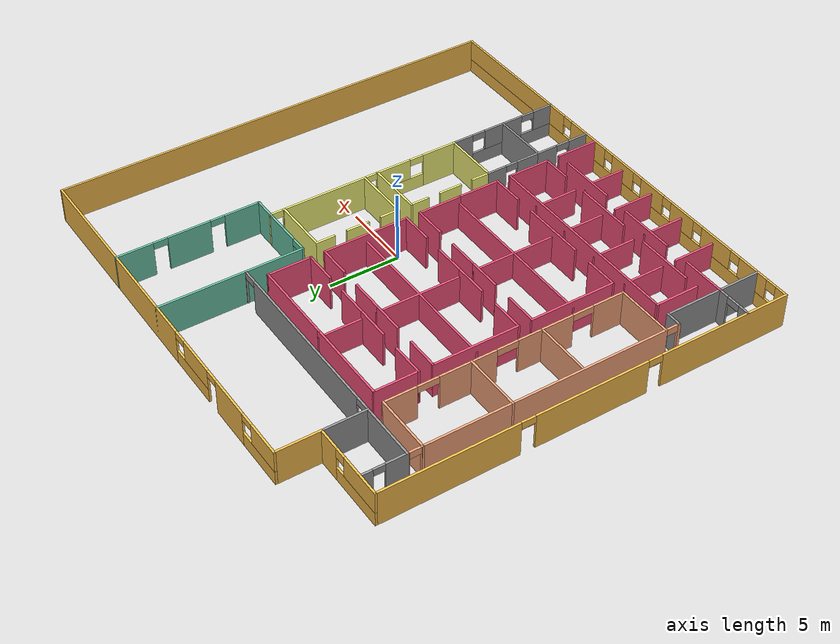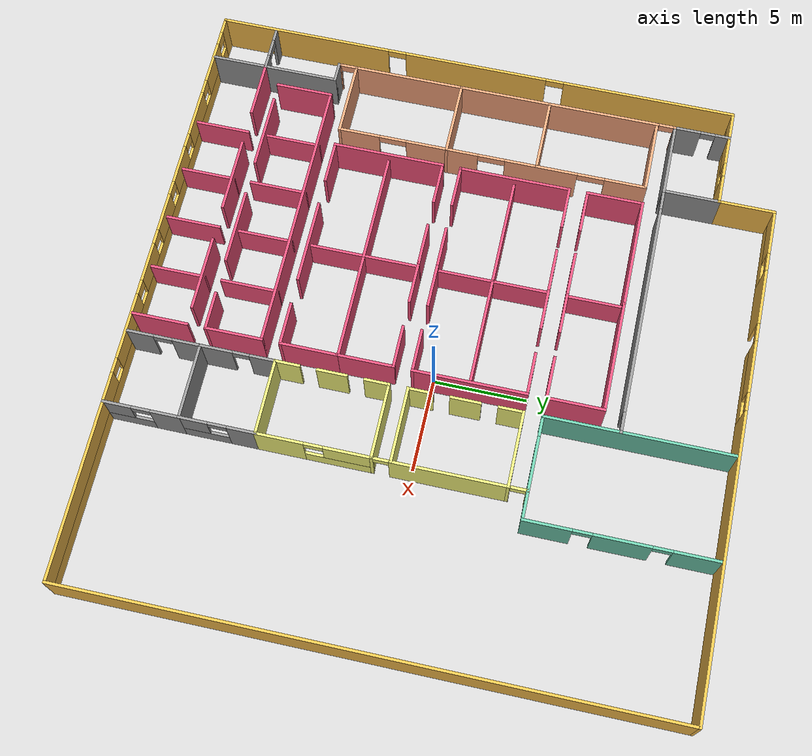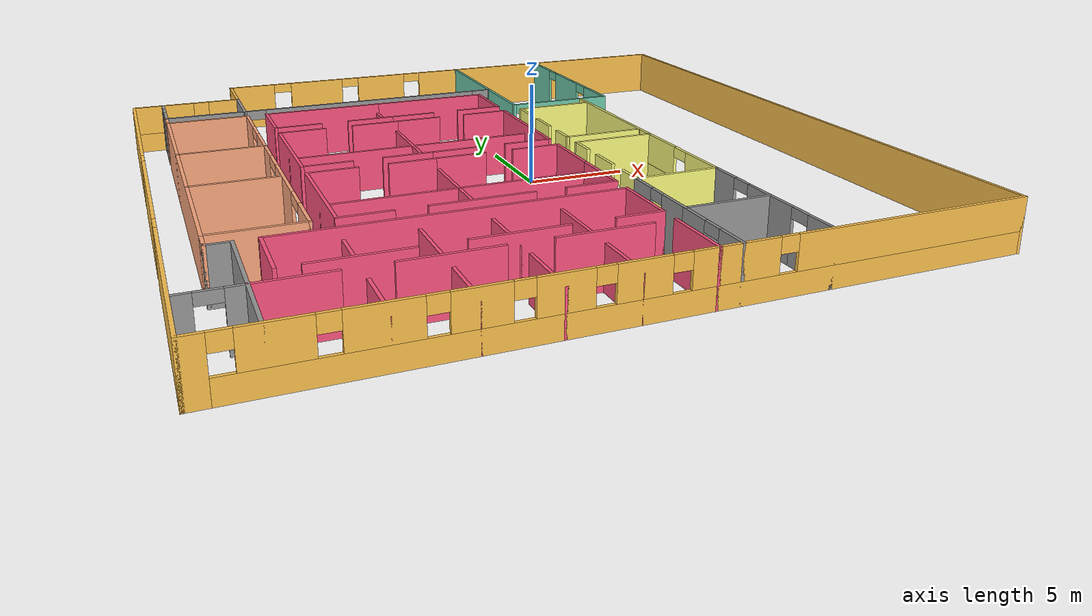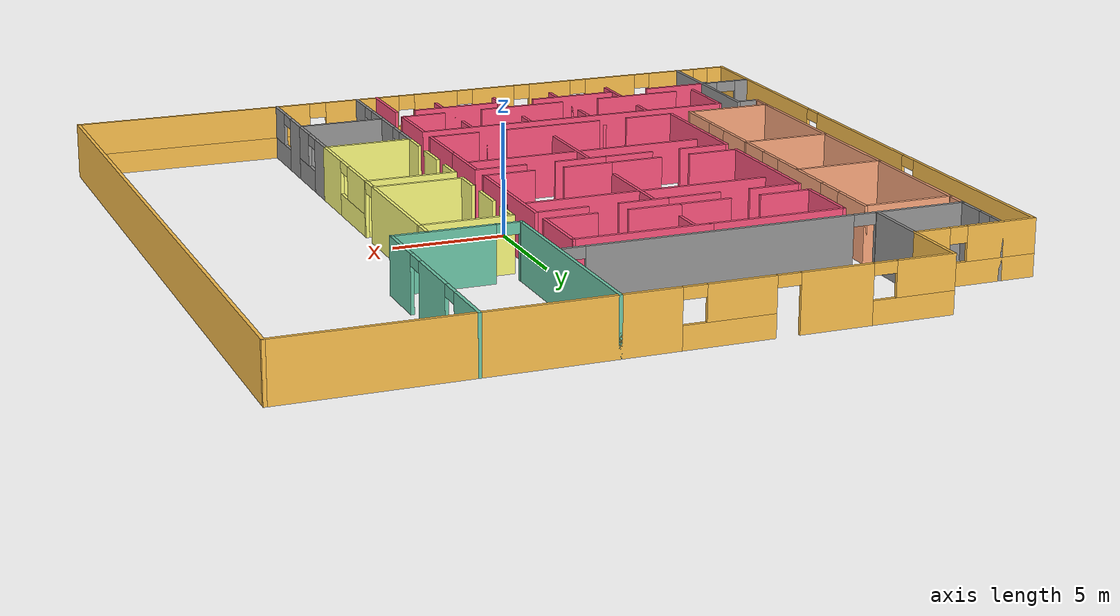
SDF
<?xml version='1.0'?>
<sdf version='1.6'>
  <model name='myWorld'>
    <pose frame=''>-1.5 0 0 0 -0 0</pose>
    <link name='Wall_0'>
      <pose frame=''>0 -16 0 0 -0 0</pose>
      <visual name='Wall_0_Visual_0'>
        <pose frame=''>-16.1125 0 1.25 0 -0 0</pose>
        <geometry>
          <box>
            <size>0.925 0.15 2.5</size>
          </box>
        </geometry>
        <material>
          <script>
            <uri>file://media/materials/scripts/gazebo.material</uri>
            <name>Gazebo/Grey</name>
          </script>
          <ambient>1 0.764706 0.305882 1</ambient>
        </material>
        <meta>
          <layer>0</layer>
        </meta>
      </visual>
      <collision name='Wall_0_Collision_0'>
        <geometry>
          <box>
            <size>0.925 0.15 2.5</size>
          </box>
        </geometry>
        <pose frame=''>-16.1125 0 1.25 0 -0 0</pose>
      </collision>
      <visual name='Wall_0_Visual_1'>
        <pose frame=''>0.4625 0 0.5 0 -0 0</pose>
        <geometry>
          <box>
            <size>32.225 0.15 1</size>
          </box>
        </geometry>
        <material>
          <script>
            <uri>file://media/materials/scripts/gazebo.material</uri>
            <name>Gazebo/Grey</name>
          </script>
          <ambient>1 0.764706 0.305882 1</ambient>
        </material>
        <meta>
          <layer>0</layer>
        </meta>
      </visual>
      <collision name='Wall_0_Collision_1'>
        <geometry>
          <box>
            <size>32.225 0.15 1</size>
          </box>
        </geometry>
        <pose frame=''>0.4625 0 0.5 0 -0 0</pose>
      </collision>
      <visual name='Wall_0_Visual_2'>
        <pose frame=''>-13.625 0 1.75 0 -0 0</pose>
        <geometry>
          <box>
            <size>2.45 0.15 1.5</size>
          </box>
        </geometry>
        <material>
          <script>
            <uri>file://media/materials/scripts/gazebo.material</uri>
            <name>Gazebo/Grey</name>
          </script>
          <ambient>1 0.764706 0.305882 1</ambient>
        </material>
        <meta>
          <layer>0</layer>
        </meta>
      </visual>
      <collision name='Wall_0_Collision_2'>
        <geometry>
          <box>
            <size>2.45 0.15 1.5</size>
          </box>
        </geometry>
        <pose frame=''>-13.625 0 1.75 0 -0 0</pose>
      </collision>
      <visual name='Wall_0_Visual_3'>
        <pose frame=''>-10.25 0 1.75 0 -0 0</pose>
        <geometry>
          <box>
            <size>2.7 0.15 1.5</size>
          </box>
        </geometry>
        <material>
          <script>
            <uri>file://media/materials/scripts/gazebo.material</uri>
            <name>Gazebo/Grey</name>
          </script>
          <ambient>1 0.764706 0.305882 1</ambient>
        </material>
        <meta>
          <layer>0</layer>
        </meta>
      </visual>
      <collision name='Wall_0_Collision_3'>
        <geometry>
          <box>
            <size>2.7 0.15 1.5</size>
          </box>
        </geometry>
        <pose frame=''>-10.25 0 1.75 0 -0 0</pose>
      </collision>
      <visual name='Wall_0_Visual_4'>
        <pose frame=''>-7 0 1.75 0 -0 0</pose>
        <geometry>
          <box>
            <size>2.2 0.15 1.5</size>
          </box>
        </geometry>
        <material>
          <script>
            <uri>file://media/materials/scripts/gazebo.material</uri>
            <name>Gazebo/Grey</name>
          </script>
          <ambient>1 0.764706 0.305882 1</ambient>
        </material>
        <meta>
          <layer>0</layer>
        </meta>
      </visual>
      <collision name='Wall_0_Collision_4'>
        <geometry>
          <box>
            <size>2.2 0.15 1.5</size>
          </box>
        </geometry>
        <pose frame=''>-7 0 1.75 0 -0 0</pose>
      </collision>
      <visual name='Wall_0_Visual_5'>
        <pose frame=''>-4 0 1.75 0 -0 0</pose>
        <geometry>
          <box>
            <size>2.2 0.15 1.5</size>
          </box>
        </geometry>
        <material>
          <script>
            <uri>file://media/materials/scripts/gazebo.material</uri>
            <name>Gazebo/Grey</name>
          </script>
          <ambient>1 0.764706 0.305882 1</ambient>
        </material>
        <meta>
          <layer>0</layer>
        </meta>
      </visual>
      <collision name='Wall_0_Collision_5'>
        <geometry>
          <box>
            <size>2.2 0.15 1.5</size>
          </box>
        </geometry>
        <pose frame=''>-4 0 1.75 0 -0 0</pose>
      </collision>
      <visual name='Wall_0_Visual_6'>
        <pose frame=''>-1 0 1.75 0 -0 0</pose>
        <geometry>
          <box>
            <size>2.2 0.15 1.5</size>
          </box>
        </geometry>
        <material>
          <script>
            <uri>file://media/materials/scripts/gazebo.material</uri>
            <name>Gazebo/Grey</name>
          </script>
          <ambient>1 0.764706 0.305882 1</ambient>
        </material>
        <meta>
          <layer>0</layer>
        </meta>
      </visual>
      <collision name='Wall_0_Collision_6'>
        <geometry>
          <box>
            <size>2.2 0.15 1.5</size>
          </box>
        </geometry>
        <pose frame=''>-1 0 1.75 0 -0 0</pose>
      </collision>
      <visual name='Wall_0_Visual_7'>
        <pose frame=''>2.75 0 1.75 0 -0 0</pose>
        <geometry>
          <box>
            <size>3.7 0.15 1.5</size>
          </box>
        </geometry>
        <material>
          <script>
            <uri>file://media/materials/scripts/gazebo.material</uri>
            <name>Gazebo/Grey</name>
          </script>
          <ambient>1 0.764706 0.305882 1</ambient>
        </material>
        <meta>
          <layer>0</layer>
        </meta>
      </visual>
      <collision name='Wall_0_Collision_7'>
        <geometry>
          <box>
            <size>3.7 0.15 1.5</size>
          </box>
        </geometry>
        <pose frame=''>2.75 0 1.75 0 -0 0</pose>
      </collision>
      <visual name='Wall_0_Visual_8'>
        <pose frame=''>10.9875 0 1.75 0 -0 0</pose>
        <geometry>
          <box>
            <size>11.175 0.15 1.5</size>
          </box>
        </geometry>
        <material>
          <script>
            <uri>file://media/materials/scripts/gazebo.material</uri>
            <name>Gazebo/Grey</name>
          </script>
          <ambient>1 0.764706 0.305882 1</ambient>
        </material>
        <meta>
          <layer>0</layer>
        </meta>
      </visual>
      <collision name='Wall_0_Collision_8'>
        <geometry>
          <box>
            <size>11.175 0.15 1.5</size>
          </box>
        </geometry>
        <pose frame=''>10.9875 0 1.75 0 -0 0</pose>
      </collision>
      <visual name='Wall_0_Visual_9'>
        <pose frame=''>-15.25 0 2.15 0 -0 0</pose>
        <geometry>
          <box>
            <size>0.8 0.15 0.7</size>
          </box>
        </geometry>
        <material>
          <script>
            <uri>file://media/materials/scripts/gazebo.material</uri>
            <name>Gazebo/Grey</name>
          </script>
          <ambient>1 0.764706 0.305882 1</ambient>
        </material>
        <meta>
          <layer>0</layer>
        </meta>
      </visual>
      <collision name='Wall_0_Collision_9'>
        <geometry>
          <box>
            <size>0.8 0.15 0.7</size>
          </box>
        </geometry>
        <pose frame=''>-15.25 0 2.15 0 -0 0</pose>
      </collision>
      <visual name='Wall_0_Visual_10'>
        <pose frame=''>-12 0 2.15 0 -0 0</pose>
        <geometry>
          <box>
            <size>0.8 0.15 0.7</size>
          </box>
        </geometry>
        <material>
          <script>
            <uri>file://media/materials/scripts/gazebo.material</uri>
            <name>Gazebo/Grey</name>
          </script>
          <ambient>1 0.764706 0.305882 1</ambient>
        </material>
        <meta>
          <layer>0</layer>
        </meta>
      </visual>
      <collision name='Wall_0_Collision_10'>
        <geometry>
          <box>
            <size>0.8 0.15 0.7</size>
          </box>
        </geometry>
        <pose frame=''>-12 0 2.15 0 -0 0</pose>
      </collision>
      <visual name='Wall_0_Visual_11'>
        <pose frame=''>-8.5 0 2.15 0 -0 0</pose>
        <geometry>
          <box>
            <size>0.8 0.15 0.7</size>
          </box>
        </geometry>
        <material>
          <script>
            <uri>file://media/materials/scripts/gazebo.material</uri>
            <name>Gazebo/Grey</name>
          </script>
          <ambient>1 0.764706 0.305882 1</ambient>
        </material>
        <meta>
          <layer>0</layer>
        </meta>
      </visual>
      <collision name='Wall_0_Collision_11'>
        <geometry>
          <box>
            <size>0.8 0.15 0.7</size>
          </box>
        </geometry>
        <pose frame=''>-8.5 0 2.15 0 -0 0</pose>
      </collision>
      <visual name='Wall_0_Visual_12'>
        <pose frame=''>-5.5 0 2.15 0 -0 0</pose>
        <geometry>
          <box>
            <size>0.8 0.15 0.7</size>
          </box>
        </geometry>
        <material>
          <script>
            <uri>file://media/materials/scripts/gazebo.material</uri>
            <name>Gazebo/Grey</name>
          </script>
          <ambient>1 0.764706 0.305882 1</ambient>
        </material>
        <meta>
          <layer>0</layer>
        </meta>
      </visual>
      <collision name='Wall_0_Collision_12'>
        <geometry>
          <box>
            <size>0.8 0.15 0.7</size>
          </box>
        </geometry>
        <pose frame=''>-5.5 0 2.15 0 -0 0</pose>
      </collision>
      <visual name='Wall_0_Visual_13'>
        <pose frame=''>-2.5 0 2.15 0 -0 0</pose>
        <geometry>
          <box>
            <size>0.8 0.15 0.7</size>
          </box>
        </geometry>
        <material>
          <script>
            <uri>file://media/materials/scripts/gazebo.material</uri>
            <name>Gazebo/Grey</name>
          </script>
          <ambient>1 0.764706 0.305882 1</ambient>
        </material>
        <meta>
          <layer>0</layer>
        </meta>
      </visual>
      <collision name='Wall_0_Collision_13'>
        <geometry>
          <box>
            <size>0.8 0.15 0.7</size>
          </box>
        </geometry>
        <pose frame=''>-2.5 0 2.15 0 -0 0</pose>
      </collision>
      <visual name='Wall_0_Visual_14'>
        <pose frame=''>0.5 0 2.15 0 -0 0</pose>
        <geometry>
          <box>
            <size>0.8 0.15 0.7</size>
          </box>
        </geometry>
        <material>
          <script>
            <uri>file://media/materials/scripts/gazebo.material</uri>
            <name>Gazebo/Grey</name>
          </script>
          <ambient>1 0.764706 0.305882 1</ambient>
        </material>
        <meta>
          <layer>0</layer>
        </meta>
      </visual>
      <collision name='Wall_0_Collision_14'>
        <geometry>
          <box>
            <size>0.8 0.15 0.7</size>
          </box>
        </geometry>
        <pose frame=''>0.5 0 2.15 0 -0 0</pose>
      </collision>
      <visual name='Wall_0_Visual_15'>
        <pose frame=''>5 0 2.15 0 -0 0</pose>
        <geometry>
          <box>
            <size>0.8 0.15 0.7</size>
          </box>
        </geometry>
        <material>
          <script>
            <uri>file://media/materials/scripts/gazebo.material</uri>
            <name>Gazebo/Grey</name>
          </script>
          <ambient>1 0.764706 0.305882 1</ambient>
        </material>
        <meta>
          <layer>0</layer>
        </meta>
      </visual>
      <collision name='Wall_0_Collision_15'>
        <geometry>
          <box>
            <size>0.8 0.15 0.7</size>
          </box>
        </geometry>
        <pose frame=''>5 0 2.15 0 -0 0</pose>
      </collision>
    </link>
    <link name='Wall_10'>
      <pose frame=''>-16.5 -1.5 0 0 0 -1.5708</pose>
      <visual name='Wall_10_Visual_0'>
        <pose frame=''>-9.7875 0 1.25 0 -0 0</pose>
        <geometry>
          <box>
            <size>9.575 0.15 2.5</size>
          </box>
        </geometry>
        <material>
          <script>
            <uri>file://media/materials/scripts/gazebo.material</uri>
            <name>Gazebo/Grey</name>
          </script>
          <ambient>1 0.764706 0.305882 1</ambient>
        </material>
        <meta>
          <layer>0</layer>
        </meta>
      </visual>
      <collision name='Wall_10_Collision_0'>
        <geometry>
          <box>
            <size>9.575 0.15 2.5</size>
          </box>
        </geometry>
        <pose frame=''>-9.7875 0 1.25 0 -0 0</pose>
      </collision>
      <visual name='Wall_10_Visual_1'>
        <pose frame=''>0 0 1.25 0 -0 0</pose>
        <geometry>
          <box>
            <size>8 0.15 2.5</size>
          </box>
        </geometry>
        <material>
          <script>
            <uri>file://media/materials/scripts/gazebo.material</uri>
            <name>Gazebo/Grey</name>
          </script>
          <ambient>1 0.764706 0.305882 1</ambient>
        </material>
        <meta>
          <layer>0</layer>
        </meta>
      </visual>
      <collision name='Wall_10_Collision_1'>
        <geometry>
          <box>
            <size>8 0.15 2.5</size>
          </box>
        </geometry>
        <pose frame=''>0 0 1.25 0 -0 0</pose>
      </collision>
      <visual name='Wall_10_Visual_2'>
        <pose frame=''>9.7875 0 1.25 0 -0 0</pose>
        <geometry>
          <box>
            <size>9.575 0.15 2.5</size>
          </box>
        </geometry>
        <material>
          <script>
            <uri>file://media/materials/scripts/gazebo.material</uri>
            <name>Gazebo/Grey</name>
          </script>
          <ambient>1 0.764706 0.305882 1</ambient>
        </material>
        <meta>
          <layer>0</layer>
        </meta>
      </visual>
      <collision name='Wall_10_Collision_2'>
        <geometry>
          <box>
            <size>9.575 0.15 2.5</size>
          </box>
        </geometry>
        <pose frame=''>9.7875 0 1.25 0 -0 0</pose>
      </collision>
      <visual name='Wall_10_Visual_3'>
        <pose frame=''>-4.5 0 2.25 0 -0 0</pose>
        <geometry>
          <box>
            <size>1 0.15 0.5</size>
          </box>
        </geometry>
        <material>
          <script>
            <uri>file://media/materials/scripts/gazebo.material</uri>
            <name>Gazebo/Grey</name>
          </script>
          <ambient>1 0.764706 0.305882 1</ambient>
        </material>
        <meta>
          <layer>0</layer>
        </meta>
      </visual>
      <collision name='Wall_10_Collision_3'>
        <geometry>
          <box>
            <size>1 0.15 0.5</size>
          </box>
        </geometry>
        <pose frame=''>-4.5 0 2.25 0 -0 0</pose>
      </collision>
      <visual name='Wall_10_Visual_4'>
        <pose frame=''>4.5 0 2.25 0 -0 0</pose>
        <geometry>
          <box>
            <size>1 0.15 0.5</size>
          </box>
        </geometry>
        <material>
          <script>
            <uri>file://media/materials/scripts/gazebo.material</uri>
            <name>Gazebo/Grey</name>
          </script>
          <ambient>1 0.764706 0.305882 1</ambient>
        </material>
        <meta>
          <layer>0</layer>
        </meta>
      </visual>
      <collision name='Wall_10_Collision_4'>
        <geometry>
          <box>
            <size>1 0.15 0.5</size>
          </box>
        </geometry>
        <pose frame=''>4.5 0 2.25 0 -0 0</pose>
      </collision>
    </link>
    <link name='Wall_100'>
      <collision name='Wall_100_Collision'>
        <geometry>
          <box>
            <size>15.15 0.15 2.5</size>
          </box>
        </geometry>
        <pose frame=''>0 0 1.25 0 -0 0</pose>
      </collision>
      <visual name='Wall_100_Visual'>
        <pose frame=''>0 0 1.25 0 -0 0</pose>
        <geometry>
          <box>
            <size>15.15 0.15 2.5</size>
          </box>
        </geometry>
        <material>
          <script>
            <uri>file://media/materials/scripts/gazebo.material</uri>
            <name>Gazebo/Grey</name>
          </script>
          <ambient>1 0.333333 0.498039 1</ambient>
        </material>
        <meta>
          <layer>0</layer>
        </meta>
      </visual>
      <pose frame=''>-5.5 -9 0 0 -0 0</pose>
    </link>
    <link name='Wall_102'>
      <collision name='Wall_102_Collision'>
        <geometry>
          <box>
            <size>3.15 0.15 2</size>
          </box>
        </geometry>
        <pose frame=''>0 0 1 0 -0 0</pose>
      </collision>
      <visual name='Wall_102_Visual'>
        <pose frame=''>0 0 1 0 -0 0</pose>
        <geometry>
          <box>
            <size>3.15 0.15 2</size>
          </box>
        </geometry>
        <material>
          <script>
            <uri>file://media/materials/scripts/gazebo.material</uri>
            <name>Gazebo/Grey</name>
          </script>
          <ambient>1 0.333333 0.498039 1</ambient>
        </material>
        <meta>
          <layer>0</layer>
        </meta>
      </visual>
      <pose frame=''>-10 -10.5 0 0 0 -1.5708</pose>
    </link>
    <link name='Wall_104'>
      <collision name='Wall_104_Collision'>
        <geometry>
          <box>
            <size>3.15 0.15 2</size>
          </box>
        </geometry>
        <pose frame=''>0 0 1 0 -0 0</pose>
      </collision>
      <visual name='Wall_104_Visual'>
        <pose frame=''>0 0 1 0 -0 0</pose>
        <geometry>
          <box>
            <size>3.15 0.15 2</size>
          </box>
        </geometry>
        <material>
          <script>
            <uri>file://media/materials/scripts/gazebo.material</uri>
            <name>Gazebo/Grey</name>
          </script>
          <ambient>1 0.333333 0.498039 1</ambient>
        </material>
        <meta>
          <layer>0</layer>
        </meta>
      </visual>
      <pose frame=''>-7 -10.5 0 0 0 -1.5708</pose>
    </link>
    <link name='Wall_106'>
      <collision name='Wall_106_Collision'>
        <geometry>
          <box>
            <size>3.15 0.15 2</size>
          </box>
        </geometry>
        <pose frame=''>0 0 1 0 -0 0</pose>
      </collision>
      <visual name='Wall_106_Visual'>
        <pose frame=''>0 0 1 0 -0 0</pose>
        <geometry>
          <box>
            <size>3.15 0.15 2</size>
          </box>
        </geometry>
        <material>
          <script>
            <uri>file://media/materials/scripts/gazebo.material</uri>
            <name>Gazebo/Grey</name>
          </script>
          <ambient>1 0.333333 0.498039 1</ambient>
        </material>
        <meta>
          <layer>0</layer>
        </meta>
      </visual>
      <pose frame=''>-4 -10.5 0 0 0 -1.5708</pose>
    </link>
    <link name='Wall_108'>
      <collision name='Wall_108_Collision'>
        <geometry>
          <box>
            <size>3.15 0.15 2</size>
          </box>
        </geometry>
        <pose frame=''>0 0 1 0 -0 0</pose>
      </collision>
      <visual name='Wall_108_Visual'>
        <pose frame=''>0 0 1 0 -0 0</pose>
        <geometry>
          <box>
            <size>3.15 0.15 2</size>
          </box>
        </geometry>
        <material>
          <script>
            <uri>file://media/materials/scripts/gazebo.material</uri>
            <name>Gazebo/Grey</name>
          </script>
          <ambient>1 0.333333 0.498039 1</ambient>
        </material>
        <meta>
          <layer>0</layer>
        </meta>
      </visual>
      <pose frame=''>-1 -10.5 0 0 0 -1.5708</pose>
    </link>
    <link name='Wall_110'>
      <collision name='Wall_110_Collision'>
        <geometry>
          <box>
            <size>3.15 0.15 2.5</size>
          </box>
        </geometry>
        <pose frame=''>0 0 1.25 0 -0 0</pose>
      </collision>
      <visual name='Wall_110_Visual'>
        <pose frame=''>0 0 1.25 0 -0 0</pose>
        <geometry>
          <box>
            <size>3.15 0.15 2.5</size>
          </box>
        </geometry>
        <material>
          <script>
            <uri>file://media/materials/scripts/gazebo.material</uri>
            <name>Gazebo/Grey</name>
          </script>
          <ambient>1 0.333333 0.498039 1</ambient>
        </material>
        <meta>
          <layer>0</layer>
        </meta>
      </visual>
      <pose frame=''>2 -10.5 0 0 0 -1.5708</pose>
    </link>
    <link name='Wall_114'>
      <collision name='Wall_114_Collision'>
        <geometry>
          <box>
            <size>3.15 0.15 2.5</size>
          </box>
        </geometry>
        <pose frame=''>0 0 1.25 0 -0 0</pose>
      </collision>
      <visual name='Wall_114_Visual'>
        <pose frame=''>0 0 1.25 0 -0 0</pose>
        <geometry>
          <box>
            <size>3.15 0.15 2.5</size>
          </box>
        </geometry>
        <material>
          <script>
            <uri>file://media/materials/scripts/gazebo.material</uri>
            <name>Gazebo/Grey</name>
          </script>
          <ambient>1 0.333333 0.498039 1</ambient>
        </material>
        <meta>
          <layer>0</layer>
        </meta>
      </visual>
      <pose frame=''>-13 -10.5 0 0 0 -1.5708</pose>
    </link>
    <link name='Wall_116'>
      <collision name='Wall_116_Collision'>
        <geometry>
          <box>
            <size>4.15 0.15 2.5</size>
          </box>
        </geometry>
        <pose frame=''>0 0 1.25 0 -0 0</pose>
      </collision>
      <visual name='Wall_116_Visual'>
        <pose frame=''>0 0 1.25 0 -0 0</pose>
        <geometry>
          <box>
            <size>4.15 0.15 2.5</size>
          </box>
        </geometry>
        <material>
          <script>
            <uri>file://media/materials/scripts/gazebo.material</uri>
            <name>Gazebo/Grey</name>
          </script>
          <ambient>1 0.333333 0.498039 1</ambient>
        </material>
        <meta>
          <layer>0</layer>
        </meta>
      </visual>
      <pose frame=''>-10 -12 0 0 -0 0</pose>
    </link>
    <link name='Wall_118'>
      <collision name='Wall_118_Collision'>
        <geometry>
          <box>
            <size>4.15 0.15 2.5</size>
          </box>
        </geometry>
        <pose frame=''>0 0 1.25 0 -0 0</pose>
      </collision>
      <visual name='Wall_118_Visual'>
        <pose frame=''>0 0 1.25 0 -0 0</pose>
        <geometry>
          <box>
            <size>4.15 0.15 2.5</size>
          </box>
        </geometry>
        <material>
          <script>
            <uri>file://media/materials/scripts/gazebo.material</uri>
            <name>Gazebo/Grey</name>
          </script>
          <ambient>1 0.333333 0.498039 1</ambient>
        </material>
        <meta>
          <layer>0</layer>
        </meta>
      </visual>
      <pose frame=''>-4 -12 0 0 -0 0</pose>
    </link>
    <link name='Wall_12'>
      <pose frame=''>-15 11.5 0 0 0 -1.5708</pose>
      <visual name='Wall_12_Visual_0'>
        <pose frame=''>-1.1475 0 1.25 0 -0 0</pose>
        <geometry>
          <box>
            <size>0.855 0.15 2.5</size>
          </box>
        </geometry>
        <material>
          <script>
            <uri>file://media/materials/scripts/gazebo.material</uri>
            <name>Gazebo/Grey</name>
          </script>
          <ambient>1 1 1 1</ambient>
        </material>
        <meta>
          <layer>0</layer>
        </meta>
      </visual>
      <collision name='Wall_12_Collision_0'>
        <geometry>
          <box>
            <size>0.855 0.15 2.5</size>
          </box>
        </geometry>
        <pose frame=''>-1.1475 0 1.25 0 -0 0</pose>
      </collision>
      <visual name='Wall_12_Visual_1'>
        <pose frame=''>0.8275 0 1.25 0 -0 0</pose>
        <geometry>
          <box>
            <size>1.495 0.15 2.5</size>
          </box>
        </geometry>
        <material>
          <script>
            <uri>file://media/materials/scripts/gazebo.material</uri>
            <name>Gazebo/Grey</name>
          </script>
          <ambient>1 1 1 1</ambient>
        </material>
        <meta>
          <layer>0</layer>
        </meta>
      </visual>
      <collision name='Wall_12_Collision_1'>
        <geometry>
          <box>
            <size>1.495 0.15 2.5</size>
          </box>
        </geometry>
        <pose frame=''>0.8275 0 1.25 0 -0 0</pose>
      </collision>
      <visual name='Wall_12_Visual_2'>
        <pose frame=''>-0.32 0 2.25 0 -0 0</pose>
        <geometry>
          <box>
            <size>0.8 0.15 0.5</size>
          </box>
        </geometry>
        <material>
          <script>
            <uri>file://media/materials/scripts/gazebo.material</uri>
            <name>Gazebo/Grey</name>
          </script>
          <ambient>1 1 1 1</ambient>
        </material>
        <meta>
          <layer>0</layer>
        </meta>
      </visual>
      <collision name='Wall_12_Collision_2'>
        <geometry>
          <box>
            <size>0.8 0.15 0.5</size>
          </box>
        </geometry>
        <pose frame=''>-0.32 0 2.25 0 -0 0</pose>
      </collision>
    </link>
    <link name='Wall_120'>
      <collision name='Wall_120_Collision'>
        <geometry>
          <box>
            <size>2.15 0.15 2.5</size>
          </box>
        </geometry>
        <pose frame=''>0 0 1.25 0 -0 0</pose>
      </collision>
      <visual name='Wall_120_Visual'>
        <pose frame=''>0 0 1.25 0 -0 0</pose>
        <geometry>
          <box>
            <size>2.15 0.15 2.5</size>
          </box>
        </geometry>
        <material>
          <script>
            <uri>file://media/materials/scripts/gazebo.material</uri>
            <name>Gazebo/Grey</name>
          </script>
          <ambient>1 0.333333 0.498039 1</ambient>
        </material>
        <meta>
          <layer>0</layer>
        </meta>
      </visual>
      <pose frame=''>1 -12 0 0 -0 0</pose>
    </link>
    <link name='Wall_126'>
      <collision name='Wall_126_Collision'>
        <geometry>
          <box>
            <size>6.15 0.15 2</size>
          </box>
        </geometry>
        <pose frame=''>0 0 1 0 -0 0</pose>
      </collision>
      <visual name='Wall_126_Visual'>
        <pose frame=''>0 0 1 0 -0 0</pose>
        <geometry>
          <box>
            <size>6.15 0.15 2</size>
          </box>
        </geometry>
        <material>
          <script>
            <uri>file://media/materials/scripts/gazebo.material</uri>
            <name>Gazebo/Grey</name>
          </script>
          <ambient>1 0.333333 0.498039 1</ambient>
        </material>
        <meta>
          <layer>0</layer>
        </meta>
      </visual>
      <pose frame=''>-1 -5 0 0 -0 0</pose>
    </link>
    <link name='Wall_127'>
      <collision name='Wall_127_Collision'>
        <geometry>
          <box>
            <size>3.15 0.15 2.5</size>
          </box>
        </geometry>
        <pose frame=''>0 0 1.25 0 -0 0</pose>
      </collision>
      <visual name='Wall_127_Visual'>
        <pose frame=''>0 0 1.25 0 -0 0</pose>
        <geometry>
          <box>
            <size>3.15 0.15 2.5</size>
          </box>
        </geometry>
        <material>
          <script>
            <uri>file://media/materials/scripts/gazebo.material</uri>
            <name>Gazebo/Grey</name>
          </script>
          <ambient>1 0.333333 0.498039 1</ambient>
        </material>
        <meta>
          <layer>0</layer>
        </meta>
      </visual>
      <pose frame=''>2 -6.5 0 0 0 -1.5708</pose>
    </link>
    <link name='Wall_128'>
      <collision name='Wall_128_Collision'>
        <geometry>
          <box>
            <size>2.4 0.15 2.5</size>
          </box>
        </geometry>
        <pose frame=''>0 0 1.25 0 -0 0</pose>
      </collision>
      <visual name='Wall_128_Visual'>
        <pose frame=''>0 0 1.25 0 -0 0</pose>
        <geometry>
          <box>
            <size>2.4 0.15 2.5</size>
          </box>
        </geometry>
        <material>
          <script>
            <uri>file://media/materials/scripts/gazebo.material</uri>
            <name>Gazebo/Grey</name>
          </script>
          <ambient>1 0.333333 0.498039 1</ambient>
        </material>
        <meta>
          <layer>0</layer>
        </meta>
      </visual>
      <pose frame=''>0.875 -8 0 0 -0 3.14159</pose>
    </link>
    <link name='Wall_130'>
      <collision name='Wall_130_Collision'>
        <geometry>
          <box>
            <size>2.4 0.15 2.5</size>
          </box>
        </geometry>
        <pose frame=''>0 0 1.25 0 -0 0</pose>
      </collision>
      <visual name='Wall_130_Visual'>
        <pose frame=''>0 0 1.25 0 -0 0</pose>
        <geometry>
          <box>
            <size>2.4 0.15 2.5</size>
          </box>
        </geometry>
        <material>
          <script>
            <uri>file://media/materials/scripts/gazebo.material</uri>
            <name>Gazebo/Grey</name>
          </script>
          <ambient>1 0.333333 0.498039 1</ambient>
        </material>
        <meta>
          <layer>0</layer>
        </meta>
      </visual>
      <pose frame=''>-2.875 -2 0 0 -0 0</pose>
    </link>
    <link name='Wall_132'>
      <collision name='Wall_132_Collision'>
        <geometry>
          <box>
            <size>2.4 0.15 2.5</size>
          </box>
        </geometry>
        <pose frame=''>0 0 1.25 0 -0 0</pose>
      </collision>
      <visual name='Wall_132_Visual'>
        <pose frame=''>0 0 1.25 0 -0 0</pose>
        <geometry>
          <box>
            <size>2.4 0.15 2.5</size>
          </box>
        </geometry>
        <material>
          <script>
            <uri>file://media/materials/scripts/gazebo.material</uri>
            <name>Gazebo/Grey</name>
          </script>
          <ambient>1 0.333333 0.498039 1</ambient>
        </material>
        <meta>
          <layer>0</layer>
        </meta>
      </visual>
      <pose frame=''>0.875 -2 0 0 -0 0</pose>
    </link>
    <link name='Wall_133'>
      <collision name='Wall_133_Collision'>
        <geometry>
          <box>
            <size>3.15 0.15 2.5</size>
          </box>
        </geometry>
        <pose frame=''>0 0 1.25 0 -0 0</pose>
      </collision>
      <visual name='Wall_133_Visual'>
        <pose frame=''>0 0 1.25 0 -0 0</pose>
        <geometry>
          <box>
            <size>3.15 0.15 2.5</size>
          </box>
        </geometry>
        <material>
          <script>
            <uri>file://media/materials/scripts/gazebo.material</uri>
            <name>Gazebo/Grey</name>
          </script>
          <ambient>1 0.333333 0.498039 1</ambient>
        </material>
        <meta>
          <layer>0</layer>
        </meta>
      </visual>
      <pose frame=''>2 -3.5 0 0 0 -1.5708</pose>
    </link>
    <link name='Wall_135'>
      <collision name='Wall_135_Collision'>
        <geometry>
          <box>
            <size>2.4 0.15 2.5</size>
          </box>
        </geometry>
        <pose frame=''>0 0 1.25 0 -0 0</pose>
      </collision>
      <visual name='Wall_135_Visual'>
        <pose frame=''>0 0 1.25 0 -0 0</pose>
        <geometry>
          <box>
            <size>2.4 0.15 2.5</size>
          </box>
        </geometry>
        <material>
          <script>
            <uri>file://media/materials/scripts/gazebo.material</uri>
            <name>Gazebo/Grey</name>
          </script>
          <ambient>1 0.333333 0.498039 1</ambient>
        </material>
        <meta>
          <layer>0</layer>
        </meta>
      </visual>
      <pose frame=''>-2.875 5 0 0 -0 0</pose>
    </link>
    <link name='Wall_137'>
      <collision name='Wall_137_Collision'>
        <geometry>
          <box>
            <size>2.4 0.15 2.5</size>
          </box>
        </geometry>
        <pose frame=''>0 0 1.25 0 -0 0</pose>
      </collision>
      <visual name='Wall_137_Visual'>
        <pose frame=''>0 0 1.25 0 -0 0</pose>
        <geometry>
          <box>
            <size>2.4 0.15 2.5</size>
          </box>
        </geometry>
        <material>
          <script>
            <uri>file://media/materials/scripts/gazebo.material</uri>
            <name>Gazebo/Grey</name>
          </script>
          <ambient>1 0.333333 0.498039 1</ambient>
        </material>
        <meta>
          <layer>0</layer>
        </meta>
      </visual>
      <pose frame=''>0.875 5 0 0 -0 0</pose>
    </link>
    <link name='Wall_138'>
      <collision name='Wall_138_Collision'>
        <geometry>
          <box>
            <size>6.15 0.15 2.5</size>
          </box>
        </geometry>
        <pose frame=''>0 0 1.25 0 -0 0</pose>
      </collision>
      <visual name='Wall_138_Visual'>
        <pose frame=''>0 0 1.25 0 -0 0</pose>
        <geometry>
          <box>
            <size>6.15 0.15 2.5</size>
          </box>
        </geometry>
        <material>
          <script>
            <uri>file://media/materials/scripts/gazebo.material</uri>
            <name>Gazebo/Grey</name>
          </script>
          <ambient>1 0.333333 0.498039 1</ambient>
        </material>
        <meta>
          <layer>0</layer>
        </meta>
      </visual>
      <pose frame=''>2 2 0 0 0 -1.5708</pose>
    </link>
    <link name='Wall_139'>
      <collision name='Wall_139_Collision'>
        <geometry>
          <box>
            <size>2.4 0.15 2.5</size>
          </box>
        </geometry>
        <pose frame=''>0 0 1.25 0 -0 0</pose>
      </collision>
      <visual name='Wall_139_Visual'>
        <pose frame=''>0 0 1.25 0 -0 0</pose>
        <geometry>
          <box>
            <size>2.4 0.15 2.5</size>
          </box>
        </geometry>
        <material>
          <script>
            <uri>file://media/materials/scripts/gazebo.material</uri>
            <name>Gazebo/Grey</name>
          </script>
          <ambient>1 0.333333 0.498039 1</ambient>
        </material>
        <meta>
          <layer>0</layer>
        </meta>
      </visual>
      <pose frame=''>0.875 -1 0 0 -0 3.14159</pose>
    </link>
    <link name='Wall_14'>
      <pose frame=''>-15 0.5 0 0 0 -1.5708</pose>
      <visual name='Wall_14_Visual_0'>
        <pose frame=''>-9.4925 0 1.25 0 -0 0</pose>
        <geometry>
          <box>
            <size>0.165 0.15 2.5</size>
          </box>
        </geometry>
        <material>
          <script>
            <uri>file://media/materials/scripts/gazebo.material</uri>
            <name>Gazebo/Grey</name>
          </script>
          <ambient>1 0.666667 0.498039 1</ambient>
        </material>
        <meta>
          <layer>0</layer>
        </meta>
      </visual>
      <collision name='Wall_14_Collision_0'>
        <geometry>
          <box>
            <size>0.165 0.15 2.5</size>
          </box>
        </geometry>
        <pose frame=''>-9.4925 0 1.25 0 -0 0</pose>
      </collision>
      <visual name='Wall_14_Visual_1'>
        <pose frame=''>-0.025 0 1.25 0 -0 0</pose>
        <geometry>
          <box>
            <size>17.17 0.15 2.5</size>
          </box>
        </geometry>
        <material>
          <script>
            <uri>file://media/materials/scripts/gazebo.material</uri>
            <name>Gazebo/Grey</name>
          </script>
          <ambient>1 0.666667 0.498039 1</ambient>
        </material>
        <meta>
          <layer>0</layer>
        </meta>
      </visual>
      <collision name='Wall_14_Collision_1'>
        <geometry>
          <box>
            <size>17.17 0.15 2.5</size>
          </box>
        </geometry>
        <pose frame=''>-0.025 0 1.25 0 -0 0</pose>
      </collision>
      <visual name='Wall_14_Visual_2'>
        <pose frame=''>9.4675 0 1.25 0 -0 0</pose>
        <geometry>
          <box>
            <size>0.215 0.15 2.5</size>
          </box>
        </geometry>
        <material>
          <script>
            <uri>file://media/materials/scripts/gazebo.material</uri>
            <name>Gazebo/Grey</name>
          </script>
          <ambient>1 0.666667 0.498039 1</ambient>
        </material>
        <meta>
          <layer>0</layer>
        </meta>
      </visual>
      <collision name='Wall_14_Collision_2'>
        <geometry>
          <box>
            <size>0.215 0.15 2.5</size>
          </box>
        </geometry>
        <pose frame=''>9.4675 0 1.25 0 -0 0</pose>
      </collision>
      <visual name='Wall_14_Visual_3'>
        <pose frame=''>-9.01 0 2.25 0 -0 0</pose>
        <geometry>
          <box>
            <size>0.8 0.15 0.5</size>
          </box>
        </geometry>
        <material>
          <script>
            <uri>file://media/materials/scripts/gazebo.material</uri>
            <name>Gazebo/Grey</name>
          </script>
          <ambient>1 0.666667 0.498039 1</ambient>
        </material>
        <meta>
          <layer>0</layer>
        </meta>
      </visual>
      <collision name='Wall_14_Collision_3'>
        <geometry>
          <box>
            <size>0.8 0.15 0.5</size>
          </box>
        </geometry>
        <pose frame=''>-9.01 0 2.25 0 -0 0</pose>
      </collision>
      <visual name='Wall_14_Visual_4'>
        <pose frame=''>8.96 0 2.25 0 -0 0</pose>
        <geometry>
          <box>
            <size>0.8 0.15 0.5</size>
          </box>
        </geometry>
        <material>
          <script>
            <uri>file://media/materials/scripts/gazebo.material</uri>
            <name>Gazebo/Grey</name>
          </script>
          <ambient>1 0.666667 0.498039 1</ambient>
        </material>
        <meta>
          <layer>0</layer>
        </meta>
      </visual>
      <collision name='Wall_14_Collision_4'>
        <geometry>
          <box>
            <size>0.8 0.15 0.5</size>
          </box>
        </geometry>
        <pose frame=''>8.96 0 2.25 0 -0 0</pose>
      </collision>
    </link>
    <link name='Wall_141'>
      <collision name='Wall_141_Collision'>
        <geometry>
          <box>
            <size>2.4 0.15 2.5</size>
          </box>
        </geometry>
        <pose frame=''>0 0 1.25 0 -0 0</pose>
      </collision>
      <visual name='Wall_141_Visual'>
        <pose frame=''>0 0 1.25 0 -0 0</pose>
        <geometry>
          <box>
            <size>2.4 0.15 2.5</size>
          </box>
        </geometry>
        <material>
          <script>
            <uri>file://media/materials/scripts/gazebo.material</uri>
            <name>Gazebo/Grey</name>
          </script>
          <ambient>1 0.333333 0.498039 1</ambient>
        </material>
        <meta>
          <layer>0</layer>
        </meta>
      </visual>
      <pose frame=''>-2.875 -1 0 0 -0 0</pose>
    </link>
    <link name='Wall_143'>
      <collision name='Wall_143_Collision'>
        <geometry>
          <box>
            <size>6.15 0.15 2.5</size>
          </box>
        </geometry>
        <pose frame=''>0 0 1.25 0 -0 0</pose>
      </collision>
      <visual name='Wall_143_Visual'>
        <pose frame=''>0 0 1.25 0 -0 0</pose>
        <geometry>
          <box>
            <size>6.15 0.15 2.5</size>
          </box>
        </geometry>
        <material>
          <script>
            <uri>file://media/materials/scripts/gazebo.material</uri>
            <name>Gazebo/Grey</name>
          </script>
          <ambient>1 0.333333 0.498039 1</ambient>
        </material>
        <meta>
          <layer>0</layer>
        </meta>
      </visual>
      <pose frame=''>-1 9 0 0 -0 0</pose>
    </link>
    <link name='Wall_144'>
      <collision name='Wall_144_Collision'>
        <geometry>
          <box>
            <size>3.15 0.15 2.5</size>
          </box>
        </geometry>
        <pose frame=''>0 0 1.25 0 -0 0</pose>
      </collision>
      <visual name='Wall_144_Visual'>
        <pose frame=''>0 0 1.25 0 -0 0</pose>
        <geometry>
          <box>
            <size>3.15 0.15 2.5</size>
          </box>
        </geometry>
        <material>
          <script>
            <uri>file://media/materials/scripts/gazebo.material</uri>
            <name>Gazebo/Grey</name>
          </script>
          <ambient>1 0.333333 0.498039 1</ambient>
        </material>
        <meta>
          <layer>0</layer>
        </meta>
      </visual>
      <pose frame=''>2 7.5 0 0 0 -1.5708</pose>
    </link>
    <link name='Wall_145'>
      <collision name='Wall_145_Collision'>
        <geometry>
          <box>
            <size>2.4 0.15 2.5</size>
          </box>
        </geometry>
        <pose frame=''>0 0 1.25 0 -0 0</pose>
      </collision>
      <visual name='Wall_145_Visual'>
        <pose frame=''>0 0 1.25 0 -0 0</pose>
        <geometry>
          <box>
            <size>2.4 0.15 2.5</size>
          </box>
        </geometry>
        <material>
          <script>
            <uri>file://media/materials/scripts/gazebo.material</uri>
            <name>Gazebo/Grey</name>
          </script>
          <ambient>1 0.333333 0.498039 1</ambient>
        </material>
        <meta>
          <layer>0</layer>
        </meta>
      </visual>
      <pose frame=''>0.875 6 0 0 -0 3.14159</pose>
    </link>
    <link name='Wall_147'>
      <collision name='Wall_147_Collision'>
        <geometry>
          <box>
            <size>2.4 0.15 2.5</size>
          </box>
        </geometry>
        <pose frame=''>0 0 1.25 0 -0 0</pose>
      </collision>
      <visual name='Wall_147_Visual'>
        <pose frame=''>0 0 1.25 0 -0 0</pose>
        <geometry>
          <box>
            <size>2.4 0.15 2.5</size>
          </box>
        </geometry>
        <material>
          <script>
            <uri>file://media/materials/scripts/gazebo.material</uri>
            <name>Gazebo/Grey</name>
          </script>
          <ambient>1 0.333333 0.498039 1</ambient>
        </material>
        <meta>
          <layer>0</layer>
        </meta>
      </visual>
      <pose frame=''>-2.875 6 0 0 -0 0</pose>
    </link>
    <link name='Wall_149'>
      <collision name='Wall_149_Collision'>
        <geometry>
          <box>
            <size>4.15 0.15 2.5</size>
          </box>
        </geometry>
        <pose frame=''>0 0 1.25 0 -0 0</pose>
      </collision>
      <visual name='Wall_149_Visual'>
        <pose frame=''>0 0 1.25 0 -0 0</pose>
        <geometry>
          <box>
            <size>4.15 0.15 2.5</size>
          </box>
        </geometry>
        <material>
          <script>
            <uri>file://media/materials/scripts/gazebo.material</uri>
            <name>Gazebo/Grey</name>
          </script>
          <ambient>1 0.666667 0.498039 1</ambient>
        </material>
        <meta>
          <layer>0</layer>
        </meta>
      </visual>
      <pose frame=''>-13 3 0 0 -0 0</pose>
    </link>
    <link name='Wall_151'>
      <pose frame=''>3 -14 0 0 -0 1.5708</pose>
      <visual name='Wall_151_Visual_0'>
        <pose frame=''>-1.2875 0 1.25 0 -0 0</pose>
        <geometry>
          <box>
            <size>1.575 0.15 2.5</size>
          </box>
        </geometry>
        <material>
          <script>
            <uri>file://media/materials/scripts/gazebo.material</uri>
            <name>Gazebo/Grey</name>
          </script>
          <ambient>1 1 1 1</ambient>
        </material>
        <meta>
          <layer>0</layer>
        </meta>
      </visual>
      <collision name='Wall_151_Collision_0'>
        <geometry>
          <box>
            <size>1.575 0.15 2.5</size>
          </box>
        </geometry>
        <pose frame=''>-1.2875 0 1.25 0 -0 0</pose>
      </collision>
      <visual name='Wall_151_Visual_1'>
        <pose frame=''>1.2875 0 1.25 0 -0 0</pose>
        <geometry>
          <box>
            <size>1.575 0.15 2.5</size>
          </box>
        </geometry>
        <material>
          <script>
            <uri>file://media/materials/scripts/gazebo.material</uri>
            <name>Gazebo/Grey</name>
          </script>
          <ambient>1 1 1 1</ambient>
        </material>
        <meta>
          <layer>0</layer>
        </meta>
      </visual>
      <collision name='Wall_151_Collision_1'>
        <geometry>
          <box>
            <size>1.575 0.15 2.5</size>
          </box>
        </geometry>
        <pose frame=''>1.2875 0 1.25 0 -0 0</pose>
      </collision>
      <visual name='Wall_151_Visual_2'>
        <pose frame=''>0 0 2.25 0 -0 0</pose>
        <geometry>
          <box>
            <size>1 0.15 0.5</size>
          </box>
        </geometry>
        <material>
          <script>
            <uri>file://media/materials/scripts/gazebo.material</uri>
            <name>Gazebo/Grey</name>
          </script>
          <ambient>1 1 1 1</ambient>
        </material>
        <meta>
          <layer>0</layer>
        </meta>
      </visual>
      <collision name='Wall_151_Collision_2'>
        <geometry>
          <box>
            <size>1 0.15 0.5</size>
          </box>
        </geometry>
        <pose frame=''>0 0 2.25 0 -0 0</pose>
      </collision>
    </link>
    <link name='Wall_152'>
      <collision name='Wall_152_Collision'>
        <geometry>
          <box>
            <size>4.15 0.15 2.5</size>
          </box>
        </geometry>
        <pose frame=''>0 0 1.25 0 -0 0</pose>
      </collision>
      <visual name='Wall_152_Visual'>
        <pose frame=''>0 0 1.25 0 -0 0</pose>
        <geometry>
          <box>
            <size>4.15 0.15 2.5</size>
          </box>
        </geometry>
        <material>
          <script>
            <uri>file://media/materials/scripts/gazebo.material</uri>
            <name>Gazebo/Grey</name>
          </script>
          <ambient>1 1 1 1</ambient>
        </material>
        <meta>
          <layer>0</layer>
        </meta>
      </visual>
      <pose frame=''>5 -12 0 0 -0 0</pose>
    </link>
    <link name='Wall_153'>
      <pose frame=''>7 -14 0 0 0 -1.5708</pose>
      <visual name='Wall_153_Visual_0'>
        <pose frame=''>-1.2825 0 1.25 0 -0 0</pose>
        <geometry>
          <box>
            <size>1.585 0.15 2.5</size>
          </box>
        </geometry>
        <material>
          <script>
            <uri>file://media/materials/scripts/gazebo.material</uri>
            <name>Gazebo/Grey</name>
          </script>
          <ambient>1 1 1 1</ambient>
        </material>
        <meta>
          <layer>0</layer>
        </meta>
      </visual>
      <collision name='Wall_153_Collision_0'>
        <geometry>
          <box>
            <size>1.585 0.15 2.5</size>
          </box>
        </geometry>
        <pose frame=''>-1.2825 0 1.25 0 -0 0</pose>
      </collision>
      <visual name='Wall_153_Visual_1'>
        <pose frame=''>0.7925 0 0.5 0 -0 0</pose>
        <geometry>
          <box>
            <size>2.565 0.15 1</size>
          </box>
        </geometry>
        <material>
          <script>
            <uri>file://media/materials/scripts/gazebo.material</uri>
            <name>Gazebo/Grey</name>
          </script>
          <ambient>1 1 1 1</ambient>
        </material>
        <meta>
          <layer>0</layer>
        </meta>
      </visual>
      <collision name='Wall_153_Collision_1'>
        <geometry>
          <box>
            <size>2.565 0.15 1</size>
          </box>
        </geometry>
        <pose frame=''>0.7925 0 0.5 0 -0 0</pose>
      </collision>
      <visual name='Wall_153_Visual_2'>
        <pose frame=''>1.2925 0 1.75 0 -0 0</pose>
        <geometry>
          <box>
            <size>1.565 0.15 1.5</size>
          </box>
        </geometry>
        <material>
          <script>
            <uri>file://media/materials/scripts/gazebo.material</uri>
            <name>Gazebo/Grey</name>
          </script>
          <ambient>1 1 1 1</ambient>
        </material>
        <meta>
          <layer>0</layer>
        </meta>
      </visual>
      <collision name='Wall_153_Collision_2'>
        <geometry>
          <box>
            <size>1.565 0.15 1.5</size>
          </box>
        </geometry>
        <pose frame=''>1.2925 0 1.75 0 -0 0</pose>
      </collision>
      <visual name='Wall_153_Visual_3'>
        <pose frame=''>0.01 0 2.25 0 -0 0</pose>
        <geometry>
          <box>
            <size>1 0.15 0.5</size>
          </box>
        </geometry>
        <material>
          <script>
            <uri>file://media/materials/scripts/gazebo.material</uri>
            <name>Gazebo/Grey</name>
          </script>
          <ambient>1 1 1 1</ambient>
        </material>
        <meta>
          <layer>0</layer>
        </meta>
      </visual>
      <collision name='Wall_153_Collision_3'>
        <geometry>
          <box>
            <size>1 0.15 0.5</size>
          </box>
        </geometry>
        <pose frame=''>0.01 0 2.25 0 -0 0</pose>
      </collision>
    </link>
    <link name='Wall_157'>
      <pose frame=''>3 -10 0 0 -0 1.5708</pose>
      <visual name='Wall_157_Visual_0'>
        <pose frame=''>-1.1775 0 1.25 0 -0 0</pose>
        <geometry>
          <box>
            <size>1.795 0.15 2.5</size>
          </box>
        </geometry>
        <material>
          <script>
            <uri>file://media/materials/scripts/gazebo.material</uri>
            <name>Gazebo/Grey</name>
          </script>
          <ambient>1 1 1 1</ambient>
        </material>
        <meta>
          <layer>0</layer>
        </meta>
      </visual>
      <collision name='Wall_157_Collision_0'>
        <geometry>
          <box>
            <size>1.795 0.15 2.5</size>
          </box>
        </geometry>
        <pose frame=''>-1.1775 0 1.25 0 -0 0</pose>
      </collision>
      <visual name='Wall_157_Visual_1'>
        <pose frame=''>1.3475 0 1.25 0 -0 0</pose>
        <geometry>
          <box>
            <size>1.455 0.15 2.5</size>
          </box>
        </geometry>
        <material>
          <script>
            <uri>file://media/materials/scripts/gazebo.material</uri>
            <name>Gazebo/Grey</name>
          </script>
          <ambient>1 1 1 1</ambient>
        </material>
        <meta>
          <layer>0</layer>
        </meta>
      </visual>
      <collision name='Wall_157_Collision_1'>
        <geometry>
          <box>
            <size>1.455 0.15 2.5</size>
          </box>
        </geometry>
        <pose frame=''>1.3475 0 1.25 0 -0 0</pose>
      </collision>
      <visual name='Wall_157_Visual_2'>
        <pose frame=''>0.17 0 2.25 0 -0 0</pose>
        <geometry>
          <box>
            <size>0.9 0.15 0.5</size>
          </box>
        </geometry>
        <material>
          <script>
            <uri>file://media/materials/scripts/gazebo.material</uri>
            <name>Gazebo/Grey</name>
          </script>
          <ambient>1 1 1 1</ambient>
        </material>
        <meta>
          <layer>0</layer>
        </meta>
      </visual>
      <collision name='Wall_157_Collision_2'>
        <geometry>
          <box>
            <size>0.9 0.15 0.5</size>
          </box>
        </geometry>
        <pose frame=''>0.17 0 2.25 0 -0 0</pose>
      </collision>
    </link>
    <link name='Wall_158'>
      <collision name='Wall_158_Collision'>
        <geometry>
          <box>
            <size>4.15 0.15 2.5</size>
          </box>
        </geometry>
        <pose frame=''>0 0 1.25 0 -0 0</pose>
      </collision>
      <visual name='Wall_158_Visual'>
        <pose frame=''>0 0 1.25 0 -0 0</pose>
        <geometry>
          <box>
            <size>4.15 0.15 2.5</size>
          </box>
        </geometry>
        <material>
          <script>
            <uri>file://media/materials/scripts/gazebo.material</uri>
            <name>Gazebo/Grey</name>
          </script>
          <ambient>1 1 0.498039 1</ambient>
        </material>
        <meta>
          <layer>0</layer>
        </meta>
      </visual>
      <pose frame=''>5 -8 0 0 -0 0</pose>
    </link>
    <link name='Wall_159'>
      <pose frame=''>7 -10 0 0 0 -1.5708</pose>
      <visual name='Wall_159_Visual_0'>
        <pose frame=''>-1.2875 0 1.25 0 -0 0</pose>
        <geometry>
          <box>
            <size>1.575 0.15 2.5</size>
          </box>
        </geometry>
        <material>
          <script>
            <uri>file://media/materials/scripts/gazebo.material</uri>
            <name>Gazebo/Grey</name>
          </script>
          <ambient>1 1 1 1</ambient>
        </material>
        <meta>
          <layer>0</layer>
        </meta>
      </visual>
      <collision name='Wall_159_Collision_0'>
        <geometry>
          <box>
            <size>1.575 0.15 2.5</size>
          </box>
        </geometry>
        <pose frame=''>-1.2875 0 1.25 0 -0 0</pose>
      </collision>
      <visual name='Wall_159_Visual_1'>
        <pose frame=''>0.7875 0 0.5 0 -0 0</pose>
        <geometry>
          <box>
            <size>2.575 0.15 1</size>
          </box>
        </geometry>
        <material>
          <script>
            <uri>file://media/materials/scripts/gazebo.material</uri>
            <name>Gazebo/Grey</name>
          </script>
          <ambient>1 1 1 1</ambient>
        </material>
        <meta>
          <layer>0</layer>
        </meta>
      </visual>
      <collision name='Wall_159_Collision_1'>
        <geometry>
          <box>
            <size>2.575 0.15 1</size>
          </box>
        </geometry>
        <pose frame=''>0.7875 0 0.5 0 -0 0</pose>
      </collision>
      <visual name='Wall_159_Visual_2'>
        <pose frame=''>1.2875 0 1.75 0 -0 0</pose>
        <geometry>
          <box>
            <size>1.575 0.15 1.5</size>
          </box>
        </geometry>
        <material>
          <script>
            <uri>file://media/materials/scripts/gazebo.material</uri>
            <name>Gazebo/Grey</name>
          </script>
          <ambient>1 1 1 1</ambient>
        </material>
        <meta>
          <layer>0</layer>
        </meta>
      </visual>
      <collision name='Wall_159_Collision_2'>
        <geometry>
          <box>
            <size>1.575 0.15 1.5</size>
          </box>
        </geometry>
        <pose frame=''>1.2875 0 1.75 0 -0 0</pose>
      </collision>
      <visual name='Wall_159_Visual_3'>
        <pose frame=''>0 0 2.25 0 -0 0</pose>
        <geometry>
          <box>
            <size>1 0.15 0.5</size>
          </box>
        </geometry>
        <material>
          <script>
            <uri>file://media/materials/scripts/gazebo.material</uri>
            <name>Gazebo/Grey</name>
          </script>
          <ambient>1 1 1 1</ambient>
        </material>
        <meta>
          <layer>0</layer>
        </meta>
      </visual>
      <collision name='Wall_159_Collision_3'>
        <geometry>
          <box>
            <size>1 0.15 0.5</size>
          </box>
        </geometry>
        <pose frame=''>0 0 2.25 0 -0 0</pose>
      </collision>
    </link>
    <link name='Wall_16'>
      <collision name='Wall_16_Collision'>
        <geometry>
          <box>
            <size>7.15 0.15 2.5</size>
          </box>
        </geometry>
        <pose frame=''>0 0 1.25 0 -0 0</pose>
      </collision>
      <visual name='Wall_16_Visual'>
        <pose frame=''>0 0 1.25 0 -0 0</pose>
        <geometry>
          <box>
            <size>7.15 0.15 2.5</size>
          </box>
        </geometry>
        <material>
          <script>
            <uri>file://media/materials/scripts/gazebo.material</uri>
            <name>Gazebo/Grey</name>
          </script>
          <ambient>1 1 1 1</ambient>
        </material>
        <meta>
          <layer>0</layer>
        </meta>
      </visual>
      <pose frame=''>-14 -12.5 0 0 0 -1.5708</pose>
    </link>
    <link name='Wall_161'>
      <pose frame=''>7 -5 0 0 -0 1.5708</pose>
      <visual name='Wall_161_Visual_0'>
        <pose frame=''>-1.7875 0 1.25 0 -0 0</pose>
        <geometry>
          <box>
            <size>2.575 0.15 2.5</size>
          </box>
        </geometry>
        <material>
          <script>
            <uri>file://media/materials/scripts/gazebo.material</uri>
            <name>Gazebo/Grey</name>
          </script>
          <ambient>1 1 0.498039 1</ambient>
        </material>
        <meta>
          <layer>0</layer>
        </meta>
      </visual>
      <collision name='Wall_161_Collision_0'>
        <geometry>
          <box>
            <size>2.575 0.15 2.5</size>
          </box>
        </geometry>
        <pose frame=''>-1.7875 0 1.25 0 -0 0</pose>
      </collision>
      <visual name='Wall_161_Visual_1'>
        <pose frame=''>1.2875 0 0.5 0 -0 0</pose>
        <geometry>
          <box>
            <size>3.575 0.15 1</size>
          </box>
        </geometry>
        <material>
          <script>
            <uri>file://media/materials/scripts/gazebo.material</uri>
            <name>Gazebo/Grey</name>
          </script>
          <ambient>1 1 0.498039 1</ambient>
        </material>
        <meta>
          <layer>0</layer>
        </meta>
      </visual>
      <collision name='Wall_161_Collision_1'>
        <geometry>
          <box>
            <size>3.575 0.15 1</size>
          </box>
        </geometry>
        <pose frame=''>1.2875 0 0.5 0 -0 0</pose>
      </collision>
      <visual name='Wall_161_Visual_2'>
        <pose frame=''>1.7875 0 1.75 0 -0 0</pose>
        <geometry>
          <box>
            <size>2.575 0.15 1.5</size>
          </box>
        </geometry>
        <material>
          <script>
            <uri>file://media/materials/scripts/gazebo.material</uri>
            <name>Gazebo/Grey</name>
          </script>
          <ambient>1 1 0.498039 1</ambient>
        </material>
        <meta>
          <layer>0</layer>
        </meta>
      </visual>
      <collision name='Wall_161_Collision_2'>
        <geometry>
          <box>
            <size>2.575 0.15 1.5</size>
          </box>
        </geometry>
        <pose frame=''>1.7875 0 1.75 0 -0 0</pose>
      </collision>
      <visual name='Wall_161_Visual_3'>
        <pose frame=''>1.7875 0 1.75 0 -0 0</pose>
        <geometry>
          <box>
            <size>2.575 0.15 1.5</size>
          </box>
        </geometry>
        <material>
          <script>
            <uri>file://media/materials/scripts/gazebo.material</uri>
            <name>Gazebo/Grey</name>
          </script>
          <ambient>1 1 0.498039 1</ambient>
        </material>
        <meta>
          <layer>0</layer>
        </meta>
      </visual>
      <collision name='Wall_161_Collision_3'>
        <geometry>
          <box>
            <size>2.575 0.15 1.5</size>
          </box>
        </geometry>
        <pose frame=''>1.7875 0 1.75 0 -0 0</pose>
      </collision>
      <visual name='Wall_161_Visual_4'>
        <pose frame=''>0 0 2.25 0 -0 0</pose>
        <geometry>
          <box>
            <size>1 0.15 0.5</size>
          </box>
        </geometry>
        <material>
          <script>
            <uri>file://media/materials/scripts/gazebo.material</uri>
            <name>Gazebo/Grey</name>
          </script>
          <ambient>1 1 0.498039 1</ambient>
        </material>
        <meta>
          <layer>0</layer>
        </meta>
      </visual>
      <collision name='Wall_161_Collision_4'>
        <geometry>
          <box>
            <size>1 0.15 0.5</size>
          </box>
        </geometry>
        <pose frame=''>0 0 2.25 0 -0 0</pose>
      </collision>
    </link>
    <link name='Wall_163'>
      <collision name='Wall_163_Collision'>
        <geometry>
          <box>
            <size>4.15 0.15 2.5</size>
          </box>
        </geometry>
        <pose frame=''>0 0 1.25 0 -0 0</pose>
      </collision>
      <visual name='Wall_163_Visual'>
        <pose frame=''>0 0 1.25 0 -0 0</pose>
        <geometry>
          <box>
            <size>4.15 0.15 2.5</size>
          </box>
        </geometry>
        <material>
          <script>
            <uri>file://media/materials/scripts/gazebo.material</uri>
            <name>Gazebo/Grey</name>
          </script>
          <ambient>1 1 0.498039 1</ambient>
        </material>
        <meta>
          <layer>0</layer>
        </meta>
      </visual>
      <pose frame=''>5 -2 0 0 -0 3.14159</pose>
    </link>
    <link name='Wall_165'>
      <collision name='Wall_165_Collision'>
        <geometry>
          <box>
            <size>1.4 0.15 2.5</size>
          </box>
        </geometry>
        <pose frame=''>0 0 1.25 0 -0 0</pose>
      </collision>
      <visual name='Wall_165_Visual'>
        <pose frame=''>0 0 1.25 0 -0 0</pose>
        <geometry>
          <box>
            <size>1.4 0.15 2.5</size>
          </box>
        </geometry>
        <material>
          <script>
            <uri>file://media/materials/scripts/gazebo.material</uri>
            <name>Gazebo/Grey</name>
          </script>
          <ambient>1 1 0.498039 1</ambient>
        </material>
        <meta>
          <layer>0</layer>
        </meta>
      </visual>
      <pose frame=''>3 -2.625 0 0 0 -1.5708</pose>
    </link>
    <link name='Wall_167'>
      <collision name='Wall_167_Collision'>
        <geometry>
          <box>
            <size>1.65 0.15 2.5</size>
          </box>
        </geometry>
        <pose frame=''>0 0 1.25 0 -0 0</pose>
      </collision>
      <visual name='Wall_167_Visual'>
        <pose frame=''>0 0 1.25 0 -0 0</pose>
        <geometry>
          <box>
            <size>1.65 0.15 2.5</size>
          </box>
        </geometry>
        <material>
          <script>
            <uri>file://media/materials/scripts/gazebo.material</uri>
            <name>Gazebo/Grey</name>
          </script>
          <ambient>1 1 0.498039 1</ambient>
        </material>
        <meta>
          <layer>0</layer>
        </meta>
      </visual>
      <pose frame=''>3 -5 0 0 0 -1.5708</pose>
    </link>
    <link name='Wall_169'>
      <collision name='Wall_169_Collision'>
        <geometry>
          <box>
            <size>1.4 0.15 2.5</size>
          </box>
        </geometry>
        <pose frame=''>0 0 1.25 0 -0 0</pose>
      </collision>
      <visual name='Wall_169_Visual'>
        <pose frame=''>0 0 1.25 0 -0 0</pose>
        <geometry>
          <box>
            <size>1.4 0.15 2.5</size>
          </box>
        </geometry>
        <material>
          <script>
            <uri>file://media/materials/scripts/gazebo.material</uri>
            <name>Gazebo/Grey</name>
          </script>
          <ambient>1 1 0.498039 1</ambient>
        </material>
        <meta>
          <layer>0</layer>
        </meta>
      </visual>
      <pose frame=''>3 -7.375 0 0 -0 1.5708</pose>
    </link>
    <link name='Wall_171'>
      <pose frame=''>7 2 0 0 -0 1.5708</pose>
      <visual name='Wall_171_Visual_0'>
        <pose frame=''>-3.9875 0 1.25 0 -0 0</pose>
        <geometry>
          <box>
            <size>0.175 0.15 2.5</size>
          </box>
        </geometry>
        <material>
          <script>
            <uri>file://media/materials/scripts/gazebo.material</uri>
            <name>Gazebo/Grey</name>
          </script>
          <ambient>1 1 0.498039 1</ambient>
        </material>
        <meta>
          <layer>0</layer>
        </meta>
      </visual>
      <collision name='Wall_171_Collision_0'>
        <geometry>
          <box>
            <size>0.175 0.15 2.5</size>
          </box>
        </geometry>
        <pose frame=''>-3.9875 0 1.25 0 -0 0</pose>
      </collision>
      <visual name='Wall_171_Visual_1'>
        <pose frame=''>-0 0 1.25 0 -0 0</pose>
        <geometry>
          <box>
            <size>6.2 0.15 2.5</size>
          </box>
        </geometry>
        <material>
          <script>
            <uri>file://media/materials/scripts/gazebo.material</uri>
            <name>Gazebo/Grey</name>
          </script>
          <ambient>1 1 0.498039 1</ambient>
        </material>
        <meta>
          <layer>0</layer>
        </meta>
      </visual>
      <collision name='Wall_171_Collision_1'>
        <geometry>
          <box>
            <size>6.2 0.15 2.5</size>
          </box>
        </geometry>
        <pose frame=''>-0 0 1.25 0 -0 0</pose>
      </collision>
      <visual name='Wall_171_Visual_2'>
        <pose frame=''>3.9875 0 1.25 0 -0 0</pose>
        <geometry>
          <box>
            <size>0.175 0.15 2.5</size>
          </box>
        </geometry>
        <material>
          <script>
            <uri>file://media/materials/scripts/gazebo.material</uri>
            <name>Gazebo/Grey</name>
          </script>
          <ambient>1 1 0.498039 1</ambient>
        </material>
        <meta>
          <layer>0</layer>
        </meta>
      </visual>
      <collision name='Wall_171_Collision_2'>
        <geometry>
          <box>
            <size>0.175 0.15 2.5</size>
          </box>
        </geometry>
        <pose frame=''>3.9875 0 1.25 0 -0 0</pose>
      </collision>
      <visual name='Wall_171_Visual_3'>
        <pose frame=''>-3.5 0 2.25 0 -0 0</pose>
        <geometry>
          <box>
            <size>0.8 0.15 0.5</size>
          </box>
        </geometry>
        <material>
          <script>
            <uri>file://media/materials/scripts/gazebo.material</uri>
            <name>Gazebo/Grey</name>
          </script>
          <ambient>1 1 0.498039 1</ambient>
        </material>
        <meta>
          <layer>0</layer>
        </meta>
      </visual>
      <collision name='Wall_171_Collision_3'>
        <geometry>
          <box>
            <size>0.8 0.15 0.5</size>
          </box>
        </geometry>
        <pose frame=''>-3.5 0 2.25 0 -0 0</pose>
      </collision>
      <visual name='Wall_171_Visual_4'>
        <pose frame=''>3.5 0 2.25 0 -0 0</pose>
        <geometry>
          <box>
            <size>0.8 0.15 0.5</size>
          </box>
        </geometry>
        <material>
          <script>
            <uri>file://media/materials/scripts/gazebo.material</uri>
            <name>Gazebo/Grey</name>
          </script>
          <ambient>1 1 0.498039 1</ambient>
        </material>
        <meta>
          <layer>0</layer>
        </meta>
      </visual>
      <collision name='Wall_171_Collision_4'>
        <geometry>
          <box>
            <size>0.8 0.15 0.5</size>
          </box>
        </geometry>
        <pose frame=''>3.5 0 2.25 0 -0 0</pose>
      </collision>
    </link>
    <link name='Wall_173'>
      <collision name='Wall_173_Collision'>
        <geometry>
          <box>
            <size>4.15 0.15 2.5</size>
          </box>
        </geometry>
        <pose frame=''>0 0 1.25 0 -0 0</pose>
      </collision>
      <visual name='Wall_173_Visual'>
        <pose frame=''>0 0 1.25 0 -0 0</pose>
        <geometry>
          <box>
            <size>4.15 0.15 2.5</size>
          </box>
        </geometry>
        <material>
          <script>
            <uri>file://media/materials/scripts/gazebo.material</uri>
            <name>Gazebo/Grey</name>
          </script>
          <ambient>1 1 0.498039 1</ambient>
        </material>
        <meta>
          <layer>0</layer>
        </meta>
      </visual>
      <pose frame=''>5 -1 0 0 -0 0</pose>
    </link>
    <link name='Wall_175'>
      <collision name='Wall_175_Collision'>
        <geometry>
          <box>
            <size>4.15 0.15 2.5</size>
          </box>
        </geometry>
        <pose frame=''>0 0 1.25 0 -0 0</pose>
      </collision>
      <visual name='Wall_175_Visual'>
        <pose frame=''>0 0 1.25 0 -0 0</pose>
        <geometry>
          <box>
            <size>4.15 0.15 2.5</size>
          </box>
        </geometry>
        <material>
          <script>
            <uri>file://media/materials/scripts/gazebo.material</uri>
            <name>Gazebo/Grey</name>
          </script>
          <ambient>1 1 0.498039 1</ambient>
        </material>
        <meta>
          <layer>0</layer>
        </meta>
      </visual>
      <pose frame=''>5 5 0 0 -0 3.14159</pose>
    </link>
    <link name='Wall_178'>
      <collision name='Wall_178_Collision'>
        <geometry>
          <box>
            <size>1.4 0.15 2.5</size>
          </box>
        </geometry>
        <pose frame=''>0 0 1.25 0 -0 0</pose>
      </collision>
      <visual name='Wall_178_Visual'>
        <pose frame=''>0 0 1.25 0 -0 0</pose>
        <geometry>
          <box>
            <size>1.4 0.15 2.5</size>
          </box>
        </geometry>
        <material>
          <script>
            <uri>file://media/materials/scripts/gazebo.material</uri>
            <name>Gazebo/Grey</name>
          </script>
          <ambient>1 1 0.498039 1</ambient>
        </material>
        <meta>
          <layer>0</layer>
        </meta>
      </visual>
      <pose frame=''>3 4.375 0 0 0 -1.5708</pose>
    </link>
    <link name='Wall_18'>
      <pose frame=''>-15.25 -13 0 0 -0 0</pose>
      <visual name='Wall_18_Visual_0'>
        <pose frame=''>-0.9125 0 1.25 0 -0 0</pose>
        <geometry>
          <box>
            <size>0.825 0.15 2.5</size>
          </box>
        </geometry>
        <material>
          <script>
            <uri>file://media/materials/scripts/gazebo.material</uri>
            <name>Gazebo/Grey</name>
          </script>
          <ambient>1 1 1 1</ambient>
        </material>
        <meta>
          <layer>0</layer>
        </meta>
      </visual>
      <collision name='Wall_18_Collision_0'>
        <geometry>
          <box>
            <size>0.825 0.15 2.5</size>
          </box>
        </geometry>
        <pose frame=''>-0.9125 0 1.25 0 -0 0</pose>
      </collision>
      <visual name='Wall_18_Visual_1'>
        <pose frame=''>0.9125 0 1.25 0 -0 0</pose>
        <geometry>
          <box>
            <size>0.825 0.15 2.5</size>
          </box>
        </geometry>
        <material>
          <script>
            <uri>file://media/materials/scripts/gazebo.material</uri>
            <name>Gazebo/Grey</name>
          </script>
          <ambient>1 1 1 1</ambient>
        </material>
        <meta>
          <layer>0</layer>
        </meta>
      </visual>
      <collision name='Wall_18_Collision_1'>
        <geometry>
          <box>
            <size>0.825 0.15 2.5</size>
          </box>
        </geometry>
        <pose frame=''>0.9125 0 1.25 0 -0 0</pose>
      </collision>
      <visual name='Wall_18_Visual_2'>
        <pose frame=''>0 0 2.25 0 -0 0</pose>
        <geometry>
          <box>
            <size>1 0.15 0.5</size>
          </box>
        </geometry>
        <material>
          <script>
            <uri>file://media/materials/scripts/gazebo.material</uri>
            <name>Gazebo/Grey</name>
          </script>
          <ambient>1 1 1 1</ambient>
        </material>
        <meta>
          <layer>0</layer>
        </meta>
      </visual>
      <collision name='Wall_18_Collision_2'>
        <geometry>
          <box>
            <size>1 0.15 0.5</size>
          </box>
        </geometry>
        <pose frame=''>0 0 2.25 0 -0 0</pose>
      </collision>
    </link>
    <link name='Wall_180'>
      <collision name='Wall_180_Collision'>
        <geometry>
          <box>
            <size>1.4 0.15 2.5</size>
          </box>
        </geometry>
        <pose frame=''>0 0 1.25 0 -0 0</pose>
      </collision>
      <visual name='Wall_180_Visual'>
        <pose frame=''>0 0 1.25 0 -0 0</pose>
        <geometry>
          <box>
            <size>1.4 0.15 2.5</size>
          </box>
        </geometry>
        <material>
          <script>
            <uri>file://media/materials/scripts/gazebo.material</uri>
            <name>Gazebo/Grey</name>
          </script>
          <ambient>1 1 0.498039 1</ambient>
        </material>
        <meta>
          <layer>0</layer>
        </meta>
      </visual>
      <pose frame=''>3 -0.375 0 0 -0 1.5708</pose>
    </link>
    <link name='Wall_182'>
      <collision name='Wall_182_Collision'>
        <geometry>
          <box>
            <size>1.65 0.15 2.5</size>
          </box>
        </geometry>
        <pose frame=''>0 0 1.25 0 -0 0</pose>
      </collision>
      <visual name='Wall_182_Visual'>
        <pose frame=''>0 0 1.25 0 -0 0</pose>
        <geometry>
          <box>
            <size>1.65 0.15 2.5</size>
          </box>
        </geometry>
        <material>
          <script>
            <uri>file://media/materials/scripts/gazebo.material</uri>
            <name>Gazebo/Grey</name>
          </script>
          <ambient>1 1 0.498039 1</ambient>
        </material>
        <meta>
          <layer>0</layer>
        </meta>
      </visual>
      <pose frame=''>3 2 0 0 -0 1.5708</pose>
    </link>
    <link name='Wall_184'>
      <pose frame=''>5.75 6 0 0 -0 3.14159</pose>
      <visual name='Wall_184_Visual_0'>
        <pose frame=''>-0.5875 0 1.25 0 -0 0</pose>
        <geometry>
          <box>
            <size>4.475 0.15 2.5</size>
          </box>
        </geometry>
        <material>
          <script>
            <uri>file://media/materials/scripts/gazebo.material</uri>
            <name>Gazebo/Grey</name>
          </script>
          <ambient>0.435294 0.796078 0.67451 1</ambient>
        </material>
        <meta>
          <layer>0</layer>
        </meta>
      </visual>
      <collision name='Wall_184_Collision_0'>
        <geometry>
          <box>
            <size>4.475 0.15 2.5</size>
          </box>
        </geometry>
        <pose frame=''>-0.5875 0 1.25 0 -0 0</pose>
      </collision>
      <visual name='Wall_184_Visual_1'>
        <pose frame=''>2.7375 0 1.25 0 -0 0</pose>
        <geometry>
          <box>
            <size>0.175 0.15 2.5</size>
          </box>
        </geometry>
        <material>
          <script>
            <uri>file://media/materials/scripts/gazebo.material</uri>
            <name>Gazebo/Grey</name>
          </script>
          <ambient>0.435294 0.796078 0.67451 1</ambient>
        </material>
        <meta>
          <layer>0</layer>
        </meta>
      </visual>
      <collision name='Wall_184_Collision_1'>
        <geometry>
          <box>
            <size>0.175 0.15 2.5</size>
          </box>
        </geometry>
        <pose frame=''>2.7375 0 1.25 0 -0 0</pose>
      </collision>
      <visual name='Wall_184_Visual_2'>
        <pose frame=''>2.15 0 2.25 0 -0 0</pose>
        <geometry>
          <box>
            <size>1 0.15 0.5</size>
          </box>
        </geometry>
        <material>
          <script>
            <uri>file://media/materials/scripts/gazebo.material</uri>
            <name>Gazebo/Grey</name>
          </script>
          <ambient>0.435294 0.796078 0.67451 1</ambient>
        </material>
        <meta>
          <layer>0</layer>
        </meta>
      </visual>
      <collision name='Wall_184_Collision_2'>
        <geometry>
          <box>
            <size>1 0.15 0.5</size>
          </box>
        </geometry>
        <pose frame=''>2.15 0 2.25 0 -0 0</pose>
      </collision>
    </link>
    <link name='Wall_185'>
      <collision name='Wall_185_Collision'>
        <geometry>
          <box>
            <size>10.15 0.15 2.5</size>
          </box>
        </geometry>
        <pose frame=''>0 0 1.25 0 -0 0</pose>
      </collision>
      <visual name='Wall_185_Visual'>
        <pose frame=''>0 0 1.25 0 -0 0</pose>
        <geometry>
          <box>
            <size>10.15 0.15 2.5</size>
          </box>
        </geometry>
        <material>
          <script>
            <uri>file://media/materials/scripts/gazebo.material</uri>
            <name>Gazebo/Grey</name>
          </script>
          <ambient>0.435294 0.796078 0.67451 1</ambient>
        </material>
        <meta>
          <layer>0</layer>
        </meta>
      </visual>
      <pose frame=''>3 11 0 0 -0 1.5708</pose>
    </link>
    <link name='Wall_187'>
      <pose frame=''>8.5 11 0 0 -0 1.5708</pose>
      <visual name='Wall_187_Visual_0'>
        <pose frame=''>-3.7875 0 1.25 0 -0 0</pose>
        <geometry>
          <box>
            <size>2.575 0.15 2.5</size>
          </box>
        </geometry>
        <material>
          <script>
            <uri>file://media/materials/scripts/gazebo.material</uri>
            <name>Gazebo/Grey</name>
          </script>
          <ambient>0.435294 0.796078 0.67451 1</ambient>
        </material>
        <meta>
          <layer>0</layer>
        </meta>
      </visual>
      <collision name='Wall_187_Collision_0'>
        <geometry>
          <box>
            <size>2.575 0.15 2.5</size>
          </box>
        </geometry>
        <pose frame=''>-3.7875 0 1.25 0 -0 0</pose>
      </collision>
      <visual name='Wall_187_Visual_1'>
        <pose frame=''>0 0 1.25 0 -0 0</pose>
        <geometry>
          <box>
            <size>3 0.15 2.5</size>
          </box>
        </geometry>
        <material>
          <script>
            <uri>file://media/materials/scripts/gazebo.material</uri>
            <name>Gazebo/Grey</name>
          </script>
          <ambient>0.435294 0.796078 0.67451 1</ambient>
        </material>
        <meta>
          <layer>0</layer>
        </meta>
      </visual>
      <collision name='Wall_187_Collision_1'>
        <geometry>
          <box>
            <size>3 0.15 2.5</size>
          </box>
        </geometry>
        <pose frame=''>0 0 1.25 0 -0 0</pose>
      </collision>
      <visual name='Wall_187_Visual_2'>
        <pose frame=''>3.7875 0 1.25 0 -0 0</pose>
        <geometry>
          <box>
            <size>2.575 0.15 2.5</size>
          </box>
        </geometry>
        <material>
          <script>
            <uri>file://media/materials/scripts/gazebo.material</uri>
            <name>Gazebo/Grey</name>
          </script>
          <ambient>0.435294 0.796078 0.67451 1</ambient>
        </material>
        <meta>
          <layer>0</layer>
        </meta>
      </visual>
      <collision name='Wall_187_Collision_2'>
        <geometry>
          <box>
            <size>2.575 0.15 2.5</size>
          </box>
        </geometry>
        <pose frame=''>3.7875 0 1.25 0 -0 0</pose>
      </collision>
      <visual name='Wall_187_Visual_3'>
        <pose frame=''>-2 0 2.25 0 -0 0</pose>
        <geometry>
          <box>
            <size>1 0.15 0.5</size>
          </box>
        </geometry>
        <material>
          <script>
            <uri>file://media/materials/scripts/gazebo.material</uri>
            <name>Gazebo/Grey</name>
          </script>
          <ambient>0.435294 0.796078 0.67451 1</ambient>
        </material>
        <meta>
          <layer>0</layer>
        </meta>
      </visual>
      <collision name='Wall_187_Collision_3'>
        <geometry>
          <box>
            <size>1 0.15 0.5</size>
          </box>
        </geometry>
        <pose frame=''>-2 0 2.25 0 -0 0</pose>
      </collision>
      <visual name='Wall_187_Visual_4'>
        <pose frame=''>2 0 2.25 0 -0 0</pose>
        <geometry>
          <box>
            <size>1 0.15 0.5</size>
          </box>
        </geometry>
        <material>
          <script>
            <uri>file://media/materials/scripts/gazebo.material</uri>
            <name>Gazebo/Grey</name>
          </script>
          <ambient>0.435294 0.796078 0.67451 1</ambient>
        </material>
        <meta>
          <layer>0</layer>
        </meta>
      </visual>
      <collision name='Wall_187_Collision_4'>
        <geometry>
          <box>
            <size>1 0.15 0.5</size>
          </box>
        </geometry>
        <pose frame=''>2 0 2.25 0 -0 0</pose>
      </collision>
    </link>
    <link name='Wall_2'>
      <collision name='Wall_2_Collision'>
        <geometry>
          <box>
            <size>32.15 0.15 2.5</size>
          </box>
        </geometry>
        <pose frame=''>0 0 1.25 0 -0 0</pose>
      </collision>
      <visual name='Wall_2_Visual'>
        <pose frame=''>0 0 1.25 0 -0 0</pose>
        <geometry>
          <box>
            <size>32.15 0.15 2.5</size>
          </box>
        </geometry>
        <material>
          <script>
            <uri>file://media/materials/scripts/gazebo.material</uri>
            <name>Gazebo/Grey</name>
          </script>
          <ambient>1 0.764706 0.305882 1</ambient>
        </material>
        <meta>
          <layer>0</layer>
        </meta>
      </visual>
      <pose frame=''>16.5 0 0 0 -0 1.5708</pose>
    </link>
    <link name='Wall_20'>
      <collision name='Wall_20_Collision'>
        <geometry>
          <box>
            <size>3.15 0.15 2.5</size>
          </box>
        </geometry>
        <pose frame=''>0 0 1.25 0 -0 0</pose>
      </collision>
      <visual name='Wall_20_Visual'>
        <pose frame=''>0 0 1.25 0 -0 0</pose>
        <geometry>
          <box>
            <size>3.15 0.15 2.5</size>
          </box>
        </geometry>
        <material>
          <script>
            <uri>file://media/materials/scripts/gazebo.material</uri>
            <name>Gazebo/Grey</name>
          </script>
          <ambient>1 1 1 1</ambient>
        </material>
        <meta>
          <layer>0</layer>
        </meta>
      </visual>
      <pose frame=''>-11 11.5 0 0 0 -1.5708</pose>
    </link>
    <link name='Wall_26'>
      <pose frame=''>-11 0.5 0 0 0 -1.5708</pose>
      <visual name='Wall_26_Visual_0'>
        <pose frame=''>-7.4125 0 1.25 0 -0 0</pose>
        <geometry>
          <box>
            <size>2.325 0.15 2.5</size>
          </box>
        </geometry>
        <material>
          <script>
            <uri>file://media/materials/scripts/gazebo.material</uri>
            <name>Gazebo/Grey</name>
          </script>
          <ambient>1 0.666667 0.498039 1</ambient>
        </material>
        <meta>
          <layer>0</layer>
        </meta>
      </visual>
      <collision name='Wall_26_Collision_0'>
        <geometry>
          <box>
            <size>2.325 0.15 2.5</size>
          </box>
        </geometry>
        <pose frame=''>-7.4125 0 1.25 0 -0 0</pose>
      </collision>
      <visual name='Wall_26_Visual_1'>
        <pose frame=''>-2.75 0 1.25 0 -0 0</pose>
        <geometry>
          <box>
            <size>4 0.15 2.5</size>
          </box>
        </geometry>
        <material>
          <script>
            <uri>file://media/materials/scripts/gazebo.material</uri>
            <name>Gazebo/Grey</name>
          </script>
          <ambient>1 0.666667 0.498039 1</ambient>
        </material>
        <meta>
          <layer>0</layer>
        </meta>
      </visual>
      <collision name='Wall_26_Collision_1'>
        <geometry>
          <box>
            <size>4 0.15 2.5</size>
          </box>
        </geometry>
        <pose frame=''>-2.75 0 1.25 0 -0 0</pose>
      </collision>
      <visual name='Wall_26_Visual_2'>
        <pose frame=''>2.75 0 1.25 0 -0 0</pose>
        <geometry>
          <box>
            <size>4 0.15 2.5</size>
          </box>
        </geometry>
        <material>
          <script>
            <uri>file://media/materials/scripts/gazebo.material</uri>
            <name>Gazebo/Grey</name>
          </script>
          <ambient>1 0.666667 0.498039 1</ambient>
        </material>
        <meta>
          <layer>0</layer>
        </meta>
      </visual>
      <collision name='Wall_26_Collision_2'>
        <geometry>
          <box>
            <size>4 0.15 2.5</size>
          </box>
        </geometry>
        <pose frame=''>2.75 0 1.25 0 -0 0</pose>
      </collision>
      <visual name='Wall_26_Visual_3'>
        <pose frame=''>7.4125 0 1.25 0 -0 0</pose>
        <geometry>
          <box>
            <size>2.325 0.15 2.5</size>
          </box>
        </geometry>
        <material>
          <script>
            <uri>file://media/materials/scripts/gazebo.material</uri>
            <name>Gazebo/Grey</name>
          </script>
          <ambient>1 0.666667 0.498039 1</ambient>
        </material>
        <meta>
          <layer>0</layer>
        </meta>
      </visual>
      <collision name='Wall_26_Collision_3'>
        <geometry>
          <box>
            <size>2.325 0.15 2.5</size>
          </box>
        </geometry>
        <pose frame=''>7.4125 0 1.25 0 -0 0</pose>
      </collision>
      <visual name='Wall_26_Visual_4'>
        <pose frame=''>-5.5 0 2.25 0 -0 0</pose>
        <geometry>
          <box>
            <size>1.5 0.15 0.5</size>
          </box>
        </geometry>
        <material>
          <script>
            <uri>file://media/materials/scripts/gazebo.material</uri>
            <name>Gazebo/Grey</name>
          </script>
          <ambient>1 0.666667 0.498039 1</ambient>
        </material>
        <meta>
          <layer>0</layer>
        </meta>
      </visual>
      <collision name='Wall_26_Collision_4'>
        <geometry>
          <box>
            <size>1.5 0.15 0.5</size>
          </box>
        </geometry>
        <pose frame=''>-5.5 0 2.25 0 -0 0</pose>
      </collision>
      <visual name='Wall_26_Visual_5'>
        <pose frame=''>0 0 2.25 0 -0 0</pose>
        <geometry>
          <box>
            <size>1.5 0.15 0.5</size>
          </box>
        </geometry>
        <material>
          <script>
            <uri>file://media/materials/scripts/gazebo.material</uri>
            <name>Gazebo/Grey</name>
          </script>
          <ambient>1 0.666667 0.498039 1</ambient>
        </material>
        <meta>
          <layer>0</layer>
        </meta>
      </visual>
      <collision name='Wall_26_Collision_5'>
        <geometry>
          <box>
            <size>1.5 0.15 0.5</size>
          </box>
        </geometry>
        <pose frame=''>0 0 2.25 0 -0 0</pose>
      </collision>
      <visual name='Wall_26_Visual_6'>
        <pose frame=''>5.5 0 2.25 0 -0 0</pose>
        <geometry>
          <box>
            <size>1.5 0.15 0.5</size>
          </box>
        </geometry>
        <material>
          <script>
            <uri>file://media/materials/scripts/gazebo.material</uri>
            <name>Gazebo/Grey</name>
          </script>
          <ambient>1 0.666667 0.498039 1</ambient>
        </material>
        <meta>
          <layer>0</layer>
        </meta>
      </visual>
      <collision name='Wall_26_Collision_6'>
        <geometry>
          <box>
            <size>1.5 0.15 0.5</size>
          </box>
        </geometry>
        <pose frame=''>5.5 0 2.25 0 -0 0</pose>
      </collision>
    </link>
    <link name='Wall_28'>
      <collision name='Wall_28_Collision'>
        <geometry>
          <box>
            <size>4.15 0.15 2.5</size>
          </box>
        </geometry>
        <pose frame=''>0 0 1.25 0 -0 0</pose>
      </collision>
      <visual name='Wall_28_Visual'>
        <pose frame=''>0 0 1.25 0 -0 0</pose>
        <geometry>
          <box>
            <size>4.15 0.15 2.5</size>
          </box>
        </geometry>
        <material>
          <script>
            <uri>file://media/materials/scripts/gazebo.material</uri>
            <name>Gazebo/Grey</name>
          </script>
          <ambient>1 0.666667 0.498039 1</ambient>
        </material>
        <meta>
          <layer>0</layer>
        </meta>
      </visual>
      <pose frame=''>-13 -2 0 0 -0 0</pose>
    </link>
    <link name='Wall_32'>
      <collision name='Wall_32_Collision'>
        <geometry>
          <box>
            <size>4.15 0.15 2.5</size>
          </box>
        </geometry>
        <pose frame=''>0 0 1.25 0 -0 0</pose>
      </collision>
      <visual name='Wall_32_Visual'>
        <pose frame=''>0 0 1.25 0 -0 0</pose>
        <geometry>
          <box>
            <size>4.15 0.15 2.5</size>
          </box>
        </geometry>
        <material>
          <script>
            <uri>file://media/materials/scripts/gazebo.material</uri>
            <name>Gazebo/Grey</name>
          </script>
          <ambient>1 0.666667 0.498039 1</ambient>
        </material>
        <meta>
          <layer>0</layer>
        </meta>
      </visual>
      <pose frame=''>-13 -8 0 0 -0 0</pose>
    </link>
    <link name='Wall_34'>
      <collision name='Wall_34_Collision'>
        <geometry>
          <box>
            <size>1.15 0.15 2.5</size>
          </box>
        </geometry>
        <pose frame=''>0 0 1.25 0 -0 0</pose>
      </collision>
      <visual name='Wall_34_Visual'>
        <pose frame=''>0 0 1.25 0 -0 0</pose>
        <geometry>
          <box>
            <size>1.15 0.15 2.5</size>
          </box>
        </geometry>
        <material>
          <script>
            <uri>file://media/materials/scripts/gazebo.material</uri>
            <name>Gazebo/Grey</name>
          </script>
          <ambient>1 1 1 1</ambient>
        </material>
        <meta>
          <layer>0</layer>
        </meta>
      </visual>
      <pose frame=''>-14.5 -9 0 0 -0 0</pose>
    </link>
    <link name='Wall_38'>
      <collision name='Wall_38_Collision'>
        <geometry>
          <box>
            <size>3.15 0.15 2.5</size>
          </box>
        </geometry>
        <pose frame=''>0 0 1.25 0 -0 0</pose>
      </collision>
      <visual name='Wall_38_Visual'>
        <pose frame=''>0 0 1.25 0 -0 0</pose>
        <geometry>
          <box>
            <size>3.15 0.15 2.5</size>
          </box>
        </geometry>
        <material>
          <script>
            <uri>file://media/materials/scripts/gazebo.material</uri>
            <name>Gazebo/Grey</name>
          </script>
          <ambient>1 0.333333 0.498039 1</ambient>
        </material>
        <meta>
          <layer>0</layer>
        </meta>
      </visual>
      <pose frame=''>-12.5 -13 0 0 -0 0</pose>
    </link>
    <link name='Wall_4'>
      <pose frame=''>2.75 16 0 0 -0 3.14159</pose>
      <visual name='Wall_4_Visual_0'>
        <pose frame=''>-5.7875 0 1.25 0 -0 0</pose>
        <geometry>
          <box>
            <size>16.075 0.15 2.5</size>
          </box>
        </geometry>
        <material>
          <script>
            <uri>file://media/materials/scripts/gazebo.material</uri>
            <name>Gazebo/Grey</name>
          </script>
          <ambient>1 0.764706 0.305882 1</ambient>
        </material>
        <meta>
          <layer>0</layer>
        </meta>
      </visual>
      <collision name='Wall_4_Collision_0'>
        <geometry>
          <box>
            <size>16.075 0.15 2.5</size>
          </box>
        </geometry>
        <pose frame=''>-5.7875 0 1.25 0 -0 0</pose>
      </collision>
      <visual name='Wall_4_Visual_1'>
        <pose frame=''>8.69912 0 1.25 0 -0 0</pose>
        <geometry>
          <box>
            <size>3.10175 0.15 2.5</size>
          </box>
        </geometry>
        <material>
          <script>
            <uri>file://media/materials/scripts/gazebo.material</uri>
            <name>Gazebo/Grey</name>
          </script>
          <ambient>1 0.764706 0.305882 1</ambient>
        </material>
        <meta>
          <layer>0</layer>
        </meta>
      </visual>
      <collision name='Wall_4_Collision_1'>
        <geometry>
          <box>
            <size>3.10175 0.15 2.5</size>
          </box>
        </geometry>
        <pose frame=''>8.69912 0 1.25 0 -0 0</pose>
      </collision>
      <visual name='Wall_4_Visual_2'>
        <pose frame=''>4.19912 0 0.5 0 -0 0</pose>
        <geometry>
          <box>
            <size>3.89825 0.15 1</size>
          </box>
        </geometry>
        <material>
          <script>
            <uri>file://media/materials/scripts/gazebo.material</uri>
            <name>Gazebo/Grey</name>
          </script>
          <ambient>1 0.764706 0.305882 1</ambient>
        </material>
        <meta>
          <layer>0</layer>
        </meta>
      </visual>
      <collision name='Wall_4_Collision_2'>
        <geometry>
          <box>
            <size>3.89825 0.15 1</size>
          </box>
        </geometry>
        <pose frame=''>4.19912 0 0.5 0 -0 0</pose>
      </collision>
      <visual name='Wall_4_Visual_3'>
        <pose frame=''>12.0375 0 0.5 0 -0 0</pose>
        <geometry>
          <box>
            <size>3.575 0.15 1</size>
          </box>
        </geometry>
        <material>
          <script>
            <uri>file://media/materials/scripts/gazebo.material</uri>
            <name>Gazebo/Grey</name>
          </script>
          <ambient>1 0.764706 0.305882 1</ambient>
        </material>
        <meta>
          <layer>0</layer>
        </meta>
      </visual>
      <collision name='Wall_4_Collision_3'>
        <geometry>
          <box>
            <size>3.575 0.15 1</size>
          </box>
        </geometry>
        <pose frame=''>12.0375 0 0.5 0 -0 0</pose>
      </collision>
      <visual name='Wall_4_Visual_4'>
        <pose frame=''>4.69912 0 1.75 0 -0 0</pose>
        <geometry>
          <box>
            <size>2.89825 0.15 1.5</size>
          </box>
        </geometry>
        <material>
          <script>
            <uri>file://media/materials/scripts/gazebo.material</uri>
            <name>Gazebo/Grey</name>
          </script>
          <ambient>1 0.764706 0.305882 1</ambient>
        </material>
        <meta>
          <layer>0</layer>
        </meta>
      </visual>
      <collision name='Wall_4_Collision_4'>
        <geometry>
          <box>
            <size>2.89825 0.15 1.5</size>
          </box>
        </geometry>
        <pose frame=''>4.69912 0 1.75 0 -0 0</pose>
      </collision>
      <visual name='Wall_4_Visual_5'>
        <pose frame=''>4.69912 0 1.75 0 -0 0</pose>
        <geometry>
          <box>
            <size>2.89825 0.15 1.5</size>
          </box>
        </geometry>
        <material>
          <script>
            <uri>file://media/materials/scripts/gazebo.material</uri>
            <name>Gazebo/Grey</name>
          </script>
          <ambient>1 0.764706 0.305882 1</ambient>
        </material>
        <meta>
          <layer>0</layer>
        </meta>
      </visual>
      <collision name='Wall_4_Collision_5'>
        <geometry>
          <box>
            <size>2.89825 0.15 1.5</size>
          </box>
        </geometry>
        <pose frame=''>4.69912 0 1.75 0 -0 0</pose>
      </collision>
      <visual name='Wall_4_Visual_6'>
        <pose frame=''>12.5375 0 1.75 0 -0 0</pose>
        <geometry>
          <box>
            <size>2.575 0.15 1.5</size>
          </box>
        </geometry>
        <material>
          <script>
            <uri>file://media/materials/scripts/gazebo.material</uri>
            <name>Gazebo/Grey</name>
          </script>
          <ambient>1 0.764706 0.305882 1</ambient>
        </material>
        <meta>
          <layer>0</layer>
        </meta>
      </visual>
      <collision name='Wall_4_Collision_6'>
        <geometry>
          <box>
            <size>2.575 0.15 1.5</size>
          </box>
        </geometry>
        <pose frame=''>12.5375 0 1.75 0 -0 0</pose>
      </collision>
      <visual name='Wall_4_Visual_7'>
        <pose frame=''>2.75 0 2.25 0 -0 0</pose>
        <geometry>
          <box>
            <size>1 0.15 0.5</size>
          </box>
        </geometry>
        <material>
          <script>
            <uri>file://media/materials/scripts/gazebo.material</uri>
            <name>Gazebo/Grey</name>
          </script>
          <ambient>1 0.764706 0.305882 1</ambient>
        </material>
        <meta>
          <layer>0</layer>
        </meta>
      </visual>
      <collision name='Wall_4_Collision_7'>
        <geometry>
          <box>
            <size>1 0.15 0.5</size>
          </box>
        </geometry>
        <pose frame=''>2.75 0 2.25 0 -0 0</pose>
      </collision>
      <visual name='Wall_4_Visual_8'>
        <pose frame=''>10.75 0 2.25 0 -0 0</pose>
        <geometry>
          <box>
            <size>1 0.15 0.5</size>
          </box>
        </geometry>
        <material>
          <script>
            <uri>file://media/materials/scripts/gazebo.material</uri>
            <name>Gazebo/Grey</name>
          </script>
          <ambient>1 0.764706 0.305882 1</ambient>
        </material>
        <meta>
          <layer>0</layer>
        </meta>
      </visual>
      <collision name='Wall_4_Collision_8'>
        <geometry>
          <box>
            <size>1 0.15 0.5</size>
          </box>
        </geometry>
        <pose frame=''>10.75 0 2.25 0 -0 0</pose>
      </collision>
      <visual name='Wall_4_Visual_9'>
        <pose frame=''>6.64825 0 2.25 0 -0 0</pose>
        <geometry>
          <box>
            <size>1 0.15 0.5</size>
          </box>
        </geometry>
        <material>
          <script>
            <uri>file://media/materials/scripts/gazebo.material</uri>
            <name>Gazebo/Grey</name>
          </script>
          <ambient>1 0.764706 0.305882 1</ambient>
        </material>
        <meta>
          <layer>0</layer>
        </meta>
      </visual>
      <collision name='Wall_4_Collision_9'>
        <geometry>
          <box>
            <size>1 0.15 0.5</size>
          </box>
        </geometry>
        <pose frame=''>6.64825 0 2.25 0 -0 0</pose>
      </collision>
      <visual name='Wall_4_Visual_10'>
        <pose frame=''>6.64825 0 2.25 0 -0 0</pose>
        <geometry>
          <box>
            <size>1 0.15 0.5</size>
          </box>
        </geometry>
        <material>
          <script>
            <uri>file://media/materials/scripts/gazebo.material</uri>
            <name>Gazebo/Grey</name>
          </script>
          <ambient>1 0.764706 0.305882 1</ambient>
        </material>
        <meta>
          <layer>0</layer>
        </meta>
      </visual>
      <collision name='Wall_4_Collision_10'>
        <geometry>
          <box>
            <size>1 0.15 0.5</size>
          </box>
        </geometry>
        <pose frame=''>6.64825 0 2.25 0 -0 0</pose>
      </collision>
    </link>
    <link name='Wall_42'>
      <pose frame=''>-6 10 0 0 -0 0</pose>
      <visual name='Wall_42_Visual_0'>
        <pose frame=''>-6.9875 0 1.25 0 -0 0</pose>
        <geometry>
          <box>
            <size>4.175 0.15 2.5</size>
          </box>
        </geometry>
        <material>
          <script>
            <uri>file://media/materials/scripts/gazebo.material</uri>
            <name>Gazebo/Grey</name>
          </script>
          <ambient>1 1 1 1</ambient>
        </material>
        <meta>
          <layer>0</layer>
        </meta>
      </visual>
      <collision name='Wall_42_Collision_0'>
        <geometry>
          <box>
            <size>4.175 0.15 2.5</size>
          </box>
        </geometry>
        <pose frame=''>-6.9875 0 1.25 0 -0 0</pose>
      </collision>
      <visual name='Wall_42_Visual_1'>
        <pose frame=''>2 0 1.25 0 -0 0</pose>
        <geometry>
          <box>
            <size>11.8 0.15 2.5</size>
          </box>
        </geometry>
        <material>
          <script>
            <uri>file://media/materials/scripts/gazebo.material</uri>
            <name>Gazebo/Grey</name>
          </script>
          <ambient>1 1 1 1</ambient>
        </material>
        <meta>
          <layer>0</layer>
        </meta>
      </visual>
      <collision name='Wall_42_Collision_1'>
        <geometry>
          <box>
            <size>11.8 0.15 2.5</size>
          </box>
        </geometry>
        <pose frame=''>2 0 1.25 0 -0 0</pose>
      </collision>
      <visual name='Wall_42_Visual_2'>
        <pose frame=''>8.9875 0 1.25 0 -0 0</pose>
        <geometry>
          <box>
            <size>0.175 0.15 2.5</size>
          </box>
        </geometry>
        <material>
          <script>
            <uri>file://media/materials/scripts/gazebo.material</uri>
            <name>Gazebo/Grey</name>
          </script>
          <ambient>1 1 1 1</ambient>
        </material>
        <meta>
          <layer>0</layer>
        </meta>
      </visual>
      <collision name='Wall_42_Collision_2'>
        <geometry>
          <box>
            <size>0.175 0.15 2.5</size>
          </box>
        </geometry>
        <pose frame=''>8.9875 0 1.25 0 -0 0</pose>
      </collision>
      <visual name='Wall_42_Visual_3'>
        <pose frame=''>-4.4 0 2.25 0 -0 0</pose>
        <geometry>
          <box>
            <size>1 0.15 0.5</size>
          </box>
        </geometry>
        <material>
          <script>
            <uri>file://media/materials/scripts/gazebo.material</uri>
            <name>Gazebo/Grey</name>
          </script>
          <ambient>1 1 1 1</ambient>
        </material>
        <meta>
          <layer>0</layer>
        </meta>
      </visual>
      <collision name='Wall_42_Collision_3'>
        <geometry>
          <box>
            <size>1 0.15 0.5</size>
          </box>
        </geometry>
        <pose frame=''>-4.4 0 2.25 0 -0 0</pose>
      </collision>
      <visual name='Wall_42_Visual_4'>
        <pose frame=''>8.4 0 2.25 0 -0 0</pose>
        <geometry>
          <box>
            <size>1 0.15 0.5</size>
          </box>
        </geometry>
        <material>
          <script>
            <uri>file://media/materials/scripts/gazebo.material</uri>
            <name>Gazebo/Grey</name>
          </script>
          <ambient>1 1 1 1</ambient>
        </material>
        <meta>
          <layer>0</layer>
        </meta>
      </visual>
      <collision name='Wall_42_Collision_4'>
        <geometry>
          <box>
            <size>1 0.15 0.5</size>
          </box>
        </geometry>
        <pose frame=''>8.4 0 2.25 0 -0 0</pose>
      </collision>
    </link>
    <link name='Wall_44'>
      <collision name='Wall_44_Collision'>
        <geometry>
          <box>
            <size>4.15 0.15 2.5</size>
          </box>
        </geometry>
        <pose frame=''>0 0 1.25 0 -0 0</pose>
      </collision>
      <visual name='Wall_44_Visual'>
        <pose frame=''>0 0 1.25 0 -0 0</pose>
        <geometry>
          <box>
            <size>4.15 0.15 2.5</size>
          </box>
        </geometry>
        <material>
          <script>
            <uri>file://media/materials/scripts/gazebo.material</uri>
            <name>Gazebo/Grey</name>
          </script>
          <ambient>1 0.666667 0.498039 1</ambient>
        </material>
        <meta>
          <layer>0</layer>
        </meta>
      </visual>
      <pose frame=''>-13 9 0 0 -0 0</pose>
    </link>
    <link name='Wall_46'>
      <collision name='Wall_46_Collision'>
        <geometry>
          <box>
            <size>6.15 0.15 2.5</size>
          </box>
        </geometry>
        <pose frame=''>0 0 1.25 0 -0 0</pose>
      </collision>
      <visual name='Wall_46_Visual'>
        <pose frame=''>0 0 1.25 0 -0 0</pose>
        <geometry>
          <box>
            <size>6.15 0.15 2.5</size>
          </box>
        </geometry>
        <material>
          <script>
            <uri>file://media/materials/scripts/gazebo.material</uri>
            <name>Gazebo/Grey</name>
          </script>
          <ambient>1 0.333333 0.498039 1</ambient>
        </material>
        <meta>
          <layer>0</layer>
        </meta>
      </visual>
      <pose frame=''>-10 -5 0 0 -0 1.5708</pose>
    </link>
    <link name='Wall_48'>
      <collision name='Wall_48_Collision'>
        <geometry>
          <box>
            <size>6.15 0.15 2</size>
          </box>
        </geometry>
        <pose frame=''>0 0 1 0 -0 0</pose>
      </collision>
      <visual name='Wall_48_Visual'>
        <pose frame=''>0 0 1 0 -0 0</pose>
        <geometry>
          <box>
            <size>6.15 0.15 2</size>
          </box>
        </geometry>
        <material>
          <script>
            <uri>file://media/materials/scripts/gazebo.material</uri>
            <name>Gazebo/Grey</name>
          </script>
          <ambient>1 0.333333 0.498039 1</ambient>
        </material>
        <meta>
          <layer>0</layer>
        </meta>
      </visual>
      <pose frame=''>-4 -5 0 0 -0 1.5708</pose>
    </link>
    <link name='Wall_50'>
      <collision name='Wall_50_Collision'>
        <geometry>
          <box>
            <size>3.15 0.15 2</size>
          </box>
        </geometry>
        <pose frame=''>0 0 1 0 -0 0</pose>
      </collision>
      <visual name='Wall_50_Visual'>
        <pose frame=''>0 0 1 0 -0 0</pose>
        <geometry>
          <box>
            <size>3.15 0.15 2</size>
          </box>
        </geometry>
        <material>
          <script>
            <uri>file://media/materials/scripts/gazebo.material</uri>
            <name>Gazebo/Grey</name>
          </script>
          <ambient>1 0.333333 0.498039 1</ambient>
        </material>
        <meta>
          <layer>0</layer>
        </meta>
      </visual>
      <pose frame=''>-10 -14.5 0 0 -0 1.5708</pose>
    </link>
    <link name='Wall_52'>
      <collision name='Wall_52_Collision'>
        <geometry>
          <box>
            <size>3.15 0.15 2</size>
          </box>
        </geometry>
        <pose frame=''>0 0 1 0 -0 0</pose>
      </collision>
      <visual name='Wall_52_Visual'>
        <pose frame=''>0 0 1 0 -0 0</pose>
        <geometry>
          <box>
            <size>3.15 0.15 2</size>
          </box>
        </geometry>
        <material>
          <script>
            <uri>file://media/materials/scripts/gazebo.material</uri>
            <name>Gazebo/Grey</name>
          </script>
          <ambient>1 0.333333 0.498039 1</ambient>
        </material>
        <meta>
          <layer>0</layer>
        </meta>
      </visual>
      <pose frame=''>-7 -14.5 0 0 -0 1.5708</pose>
    </link>
    <link name='Wall_57'>
      <collision name='Wall_57_Collision'>
        <geometry>
          <box>
            <size>3.15 0.15 2</size>
          </box>
        </geometry>
        <pose frame=''>0 0 1 0 -0 0</pose>
      </collision>
      <visual name='Wall_57_Visual'>
        <pose frame=''>0 0 1 0 -0 0</pose>
        <geometry>
          <box>
            <size>3.15 0.15 2</size>
          </box>
        </geometry>
        <material>
          <script>
            <uri>file://media/materials/scripts/gazebo.material</uri>
            <name>Gazebo/Grey</name>
          </script>
          <ambient>1 0.333333 0.498039 1</ambient>
        </material>
        <meta>
          <layer>0</layer>
        </meta>
      </visual>
      <pose frame=''>-4 -14.5 0 0 -0 1.5708</pose>
    </link>
    <link name='Wall_59'>
      <collision name='Wall_59_Collision'>
        <geometry>
          <box>
            <size>4.15 0.15 2.5</size>
          </box>
        </geometry>
        <pose frame=''>0 0 1.25 0 -0 0</pose>
      </collision>
      <visual name='Wall_59_Visual'>
        <pose frame=''>0 0 1.25 0 -0 0</pose>
        <geometry>
          <box>
            <size>4.15 0.15 2.5</size>
          </box>
        </geometry>
        <material>
          <script>
            <uri>file://media/materials/scripts/gazebo.material</uri>
            <name>Gazebo/Grey</name>
          </script>
          <ambient>1 0.333333 0.498039 1</ambient>
        </material>
        <meta>
          <layer>0</layer>
        </meta>
      </visual>
      <pose frame=''>-7 -13 0 0 -0 0</pose>
    </link>
    <link name='Wall_6'>
      <collision name='Wall_6_Collision'>
        <geometry>
          <box>
            <size>3.15 0.15 2.5</size>
          </box>
        </geometry>
        <pose frame=''>0 0 1.25 0 -0 0</pose>
      </collision>
      <visual name='Wall_6_Visual'>
        <pose frame=''>0 0 1.25 0 -0 0</pose>
        <geometry>
          <box>
            <size>3.15 0.15 2.5</size>
          </box>
        </geometry>
        <material>
          <script>
            <uri>file://media/materials/scripts/gazebo.material</uri>
            <name>Gazebo/Grey</name>
          </script>
          <ambient>1 0.764706 0.305882 1</ambient>
        </material>
        <meta>
          <layer>0</layer>
        </meta>
      </visual>
      <pose frame=''>-11 14.5 0 0 0 -1.5708</pose>
    </link>
    <link name='Wall_64'>
      <collision name='Wall_64_Collision'>
        <geometry>
          <box>
            <size>3.15 0.15 2</size>
          </box>
        </geometry>
        <pose frame=''>0 0 1 0 -0 0</pose>
      </collision>
      <visual name='Wall_64_Visual'>
        <pose frame=''>0 0 1 0 -0 0</pose>
        <geometry>
          <box>
            <size>3.15 0.15 2</size>
          </box>
        </geometry>
        <material>
          <script>
            <uri>file://media/materials/scripts/gazebo.material</uri>
            <name>Gazebo/Grey</name>
          </script>
          <ambient>1 0.333333 0.498039 1</ambient>
        </material>
        <meta>
          <layer>0</layer>
        </meta>
      </visual>
      <pose frame=''>-1 -14.5 0 0 -0 1.5708</pose>
    </link>
    <link name='Wall_68'>
      <collision name='Wall_68_Collision'>
        <geometry>
          <box>
            <size>4.15 0.15 2.5</size>
          </box>
        </geometry>
        <pose frame=''>0 0 1.25 0 -0 0</pose>
      </collision>
      <visual name='Wall_68_Visual'>
        <pose frame=''>0 0 1.25 0 -0 0</pose>
        <geometry>
          <box>
            <size>4.15 0.15 2.5</size>
          </box>
        </geometry>
        <material>
          <script>
            <uri>file://media/materials/scripts/gazebo.material</uri>
            <name>Gazebo/Grey</name>
          </script>
          <ambient>1 0.333333 0.498039 1</ambient>
        </material>
        <meta>
          <layer>0</layer>
        </meta>
      </visual>
      <pose frame=''>-1 -13 0 0 -0 0</pose>
    </link>
    <link name='Wall_70'>
      <collision name='Wall_70_Collision'>
        <geometry>
          <box>
            <size>3.15 0.15 2.5</size>
          </box>
        </geometry>
        <pose frame=''>0 0 1.25 0 -0 0</pose>
      </collision>
      <visual name='Wall_70_Visual'>
        <pose frame=''>0 0 1.25 0 -0 0</pose>
        <geometry>
          <box>
            <size>3.15 0.15 2.5</size>
          </box>
        </geometry>
        <material>
          <script>
            <uri>file://media/materials/scripts/gazebo.material</uri>
            <name>Gazebo/Grey</name>
          </script>
          <ambient>1 0.333333 0.498039 1</ambient>
        </material>
        <meta>
          <layer>0</layer>
        </meta>
      </visual>
      <pose frame=''>2 -14.5 0 0 -0 1.5708</pose>
    </link>
    <link name='Wall_72'>
      <collision name='Wall_72_Collision'>
        <geometry>
          <box>
            <size>6.15 0.15 2</size>
          </box>
        </geometry>
        <pose frame=''>0 0 1 0 -0 0</pose>
      </collision>
      <visual name='Wall_72_Visual'>
        <pose frame=''>0 0 1 0 -0 0</pose>
        <geometry>
          <box>
            <size>6.15 0.15 2</size>
          </box>
        </geometry>
        <material>
          <script>
            <uri>file://media/materials/scripts/gazebo.material</uri>
            <name>Gazebo/Grey</name>
          </script>
          <ambient>1 0.333333 0.498039 1</ambient>
        </material>
        <meta>
          <layer>0</layer>
        </meta>
      </visual>
      <pose frame=''>-7 -5 0 0 -0 0</pose>
    </link>
    <link name='Wall_74'>
      <collision name='Wall_74_Collision'>
        <geometry>
          <box>
            <size>2.4 0.15 2.5</size>
          </box>
        </geometry>
        <pose frame=''>0 0 1.25 0 -0 0</pose>
      </collision>
      <visual name='Wall_74_Visual'>
        <pose frame=''>0 0 1.25 0 -0 0</pose>
        <geometry>
          <box>
            <size>2.4 0.15 2.5</size>
          </box>
        </geometry>
        <material>
          <script>
            <uri>file://media/materials/scripts/gazebo.material</uri>
            <name>Gazebo/Grey</name>
          </script>
          <ambient>1 0.333333 0.498039 1</ambient>
        </material>
        <meta>
          <layer>0</layer>
        </meta>
      </visual>
      <pose frame=''>-8.875 -8 0 0 -0 0</pose>
    </link>
    <link name='Wall_76'>
      <collision name='Wall_76_Collision'>
        <geometry>
          <box>
            <size>4.65 0.15 2.5</size>
          </box>
        </geometry>
        <pose frame=''>0 0 1.25 0 -0 0</pose>
      </collision>
      <visual name='Wall_76_Visual'>
        <pose frame=''>0 0 1.25 0 -0 0</pose>
        <geometry>
          <box>
            <size>4.65 0.15 2.5</size>
          </box>
        </geometry>
        <material>
          <script>
            <uri>file://media/materials/scripts/gazebo.material</uri>
            <name>Gazebo/Grey</name>
          </script>
          <ambient>1 0.333333 0.498039 1</ambient>
        </material>
        <meta>
          <layer>0</layer>
        </meta>
      </visual>
      <pose frame=''>-4 -8 0 0 -0 0</pose>
    </link>
    <link name='Wall_78'>
      <collision name='Wall_78_Collision'>
        <geometry>
          <box>
            <size>2.4 0.15 2.5</size>
          </box>
        </geometry>
        <pose frame=''>0 0 1.25 0 -0 0</pose>
      </collision>
      <visual name='Wall_78_Visual'>
        <pose frame=''>0 0 1.25 0 -0 0</pose>
        <geometry>
          <box>
            <size>2.4 0.15 2.5</size>
          </box>
        </geometry>
        <material>
          <script>
            <uri>file://media/materials/scripts/gazebo.material</uri>
            <name>Gazebo/Grey</name>
          </script>
          <ambient>1 0.333333 0.498039 1</ambient>
        </material>
        <meta>
          <layer>0</layer>
        </meta>
      </visual>
      <pose frame=''>-8.875 -2 0 0 -0 0</pose>
    </link>
    <link name='Wall_8'>
      <pose frame=''>-13.75 13 0 0 -0 3.14159</pose>
      <visual name='Wall_8_Visual_0'>
        <pose frame=''>-1.9875 0 1.25 0 -0 0</pose>
        <geometry>
          <box>
            <size>1.675 0.15 2.5</size>
          </box>
        </geometry>
        <material>
          <script>
            <uri>file://media/materials/scripts/gazebo.material</uri>
            <name>Gazebo/Grey</name>
          </script>
          <ambient>1 0.764706 0.305882 1</ambient>
        </material>
        <meta>
          <layer>0</layer>
        </meta>
      </visual>
      <collision name='Wall_8_Collision_0'>
        <geometry>
          <box>
            <size>1.675 0.15 2.5</size>
          </box>
        </geometry>
        <pose frame=''>-1.9875 0 1.25 0 -0 0</pose>
      </collision>
      <visual name='Wall_8_Visual_1'>
        <pose frame=''>0.8375 0 0.5 0 -0 0</pose>
        <geometry>
          <box>
            <size>3.975 0.15 1</size>
          </box>
        </geometry>
        <material>
          <script>
            <uri>file://media/materials/scripts/gazebo.material</uri>
            <name>Gazebo/Grey</name>
          </script>
          <ambient>1 0.764706 0.305882 1</ambient>
        </material>
        <meta>
          <layer>0</layer>
        </meta>
      </visual>
      <collision name='Wall_8_Collision_1'>
        <geometry>
          <box>
            <size>3.975 0.15 1</size>
          </box>
        </geometry>
        <pose frame=''>0.8375 0 0.5 0 -0 0</pose>
      </collision>
      <visual name='Wall_8_Visual_2'>
        <pose frame=''>1.2375 0 1.75 0 -0 0</pose>
        <geometry>
          <box>
            <size>3.175 0.15 1.5</size>
          </box>
        </geometry>
        <material>
          <script>
            <uri>file://media/materials/scripts/gazebo.material</uri>
            <name>Gazebo/Grey</name>
          </script>
          <ambient>1 0.764706 0.305882 1</ambient>
        </material>
        <meta>
          <layer>0</layer>
        </meta>
      </visual>
      <collision name='Wall_8_Collision_2'>
        <geometry>
          <box>
            <size>3.175 0.15 1.5</size>
          </box>
        </geometry>
        <pose frame=''>1.2375 0 1.75 0 -0 0</pose>
      </collision>
      <visual name='Wall_8_Visual_3'>
        <pose frame=''>-0.75 0 2.15 0 -0 0</pose>
        <geometry>
          <box>
            <size>0.8 0.15 0.7</size>
          </box>
        </geometry>
        <material>
          <script>
            <uri>file://media/materials/scripts/gazebo.material</uri>
            <name>Gazebo/Grey</name>
          </script>
          <ambient>1 0.764706 0.305882 1</ambient>
        </material>
        <meta>
          <layer>0</layer>
        </meta>
      </visual>
      <collision name='Wall_8_Collision_3'>
        <geometry>
          <box>
            <size>0.8 0.15 0.7</size>
          </box>
        </geometry>
        <pose frame=''>-0.75 0 2.15 0 -0 0</pose>
      </collision>
    </link>
    <link name='Wall_80'>
      <collision name='Wall_80_Collision'>
        <geometry>
          <box>
            <size>2.4 0.15 2.5</size>
          </box>
        </geometry>
        <pose frame=''>0 0 1.25 0 -0 0</pose>
      </collision>
      <visual name='Wall_80_Visual'>
        <pose frame=''>0 0 1.25 0 -0 0</pose>
        <geometry>
          <box>
            <size>2.4 0.15 2.5</size>
          </box>
        </geometry>
        <material>
          <script>
            <uri>file://media/materials/scripts/gazebo.material</uri>
            <name>Gazebo/Grey</name>
          </script>
          <ambient>1 0.333333 0.498039 1</ambient>
        </material>
        <meta>
          <layer>0</layer>
        </meta>
      </visual>
      <pose frame=''>-5.125 -2 0 0 -0 0</pose>
    </link>
    <link name='Wall_82'>
      <collision name='Wall_82_Collision'>
        <geometry>
          <box>
            <size>2.4 0.15 2.5</size>
          </box>
        </geometry>
        <pose frame=''>0 0 1.25 0 -0 0</pose>
      </collision>
      <visual name='Wall_82_Visual'>
        <pose frame=''>0 0 1.25 0 -0 0</pose>
        <geometry>
          <box>
            <size>2.4 0.15 2.5</size>
          </box>
        </geometry>
        <material>
          <script>
            <uri>file://media/materials/scripts/gazebo.material</uri>
            <name>Gazebo/Grey</name>
          </script>
          <ambient>1 0.333333 0.498039 1</ambient>
        </material>
        <meta>
          <layer>0</layer>
        </meta>
      </visual>
      <pose frame=''>-5.125 -1 0 0 -0 0</pose>
    </link>
    <link name='Wall_83'>
      <collision name='Wall_83_Collision'>
        <geometry>
          <box>
            <size>6.15 0.15 2</size>
          </box>
        </geometry>
        <pose frame=''>0 0 1 0 -0 0</pose>
      </collision>
      <visual name='Wall_83_Visual'>
        <pose frame=''>0 0 1 0 -0 0</pose>
        <geometry>
          <box>
            <size>6.15 0.15 2</size>
          </box>
        </geometry>
        <material>
          <script>
            <uri>file://media/materials/scripts/gazebo.material</uri>
            <name>Gazebo/Grey</name>
          </script>
          <ambient>1 0.333333 0.498039 1</ambient>
        </material>
        <meta>
          <layer>0</layer>
        </meta>
      </visual>
      <pose frame=''>-4 2 0 0 -0 1.5708</pose>
    </link>
    <link name='Wall_86'>
      <collision name='Wall_86_Collision'>
        <geometry>
          <box>
            <size>12.15 0.15 2</size>
          </box>
        </geometry>
        <pose frame=''>0 0 1 0 -0 0</pose>
      </collision>
      <visual name='Wall_86_Visual'>
        <pose frame=''>0 0 1 0 -0 0</pose>
        <geometry>
          <box>
            <size>12.15 0.15 2</size>
          </box>
        </geometry>
        <material>
          <script>
            <uri>file://media/materials/scripts/gazebo.material</uri>
            <name>Gazebo/Grey</name>
          </script>
          <ambient>1 0.333333 0.498039 1</ambient>
        </material>
        <meta>
          <layer>0</layer>
        </meta>
      </visual>
      <pose frame=''>-4 2 0 0 -0 0</pose>
    </link>
    <link name='Wall_88'>
      <collision name='Wall_88_Collision'>
        <geometry>
          <box>
            <size>2.4 0.15 2.5</size>
          </box>
        </geometry>
        <pose frame=''>0 0 1.25 0 -0 0</pose>
      </collision>
      <visual name='Wall_88_Visual'>
        <pose frame=''>0 0 1.25 0 -0 0</pose>
        <geometry>
          <box>
            <size>2.4 0.15 2.5</size>
          </box>
        </geometry>
        <material>
          <script>
            <uri>file://media/materials/scripts/gazebo.material</uri>
            <name>Gazebo/Grey</name>
          </script>
          <ambient>1 0.333333 0.498039 1</ambient>
        </material>
        <meta>
          <layer>0</layer>
        </meta>
      </visual>
      <pose frame=''>-8.875 -1 0 0 -0 3.14159</pose>
    </link>
    <link name='Wall_89'>
      <collision name='Wall_89_Collision'>
        <geometry>
          <box>
            <size>6.15 0.15 2.5</size>
          </box>
        </geometry>
        <pose frame=''>0 0 1.25 0 -0 0</pose>
      </collision>
      <visual name='Wall_89_Visual'>
        <pose frame=''>0 0 1.25 0 -0 0</pose>
        <geometry>
          <box>
            <size>6.15 0.15 2.5</size>
          </box>
        </geometry>
        <material>
          <script>
            <uri>file://media/materials/scripts/gazebo.material</uri>
            <name>Gazebo/Grey</name>
          </script>
          <ambient>1 0.333333 0.498039 1</ambient>
        </material>
        <meta>
          <layer>0</layer>
        </meta>
      </visual>
      <pose frame=''>-10 2 0 0 -0 1.5708</pose>
    </link>
    <link name='Wall_90'>
      <collision name='Wall_90_Collision'>
        <geometry>
          <box>
            <size>2.4 0.15 2.5</size>
          </box>
        </geometry>
        <pose frame=''>0 0 1.25 0 -0 0</pose>
      </collision>
      <visual name='Wall_90_Visual'>
        <pose frame=''>0 0 1.25 0 -0 0</pose>
        <geometry>
          <box>
            <size>2.4 0.15 2.5</size>
          </box>
        </geometry>
        <material>
          <script>
            <uri>file://media/materials/scripts/gazebo.material</uri>
            <name>Gazebo/Grey</name>
          </script>
          <ambient>1 0.333333 0.498039 1</ambient>
        </material>
        <meta>
          <layer>0</layer>
        </meta>
      </visual>
      <pose frame=''>-8.875 5 0 0 -0 0</pose>
    </link>
    <link name='Wall_92'>
      <collision name='Wall_92_Collision'>
        <geometry>
          <box>
            <size>2.4 0.15 2.5</size>
          </box>
        </geometry>
        <pose frame=''>0 0 1.25 0 -0 0</pose>
      </collision>
      <visual name='Wall_92_Visual'>
        <pose frame=''>0 0 1.25 0 -0 0</pose>
        <geometry>
          <box>
            <size>2.4 0.15 2.5</size>
          </box>
        </geometry>
        <material>
          <script>
            <uri>file://media/materials/scripts/gazebo.material</uri>
            <name>Gazebo/Grey</name>
          </script>
          <ambient>1 0.333333 0.498039 1</ambient>
        </material>
        <meta>
          <layer>0</layer>
        </meta>
      </visual>
      <pose frame=''>-5.125 5 0 0 -0 0</pose>
    </link>
    <link name='Wall_94'>
      <collision name='Wall_94_Collision'>
        <geometry>
          <box>
            <size>2.4 0.15 2.5</size>
          </box>
        </geometry>
        <pose frame=''>0 0 1.25 0 -0 0</pose>
      </collision>
      <visual name='Wall_94_Visual'>
        <pose frame=''>0 0 1.25 0 -0 0</pose>
        <geometry>
          <box>
            <size>2.4 0.15 2.5</size>
          </box>
        </geometry>
        <material>
          <script>
            <uri>file://media/materials/scripts/gazebo.material</uri>
            <name>Gazebo/Grey</name>
          </script>
          <ambient>1 0.333333 0.498039 1</ambient>
        </material>
        <meta>
          <layer>0</layer>
        </meta>
      </visual>
      <pose frame=''>-8.875 6 0 0 -0 3.14159</pose>
    </link>
    <link name='Wall_95'>
      <collision name='Wall_95_Collision'>
        <geometry>
          <box>
            <size>3.15 0.15 2.5</size>
          </box>
        </geometry>
        <pose frame=''>0 0 1.25 0 -0 0</pose>
      </collision>
      <visual name='Wall_95_Visual'>
        <pose frame=''>0 0 1.25 0 -0 0</pose>
        <geometry>
          <box>
            <size>3.15 0.15 2.5</size>
          </box>
        </geometry>
        <material>
          <script>
            <uri>file://media/materials/scripts/gazebo.material</uri>
            <name>Gazebo/Grey</name>
          </script>
          <ambient>1 0.333333 0.498039 1</ambient>
        </material>
        <meta>
          <layer>0</layer>
        </meta>
      </visual>
      <pose frame=''>-10 7.5 0 0 -0 1.5708</pose>
    </link>
    <link name='Wall_96'>
      <collision name='Wall_96_Collision'>
        <geometry>
          <box>
            <size>6.15 0.15 2.5</size>
          </box>
        </geometry>
        <pose frame=''>0 0 1.25 0 -0 0</pose>
      </collision>
      <visual name='Wall_96_Visual'>
        <pose frame=''>0 0 1.25 0 -0 0</pose>
        <geometry>
          <box>
            <size>6.15 0.15 2.5</size>
          </box>
        </geometry>
        <material>
          <script>
            <uri>file://media/materials/scripts/gazebo.material</uri>
            <name>Gazebo/Grey</name>
          </script>
          <ambient>1 0.333333 0.498039 1</ambient>
        </material>
        <meta>
          <layer>0</layer>
        </meta>
      </visual>
      <pose frame=''>-7 9 0 0 -0 0</pose>
    </link>
    <link name='Wall_97'>
      <collision name='Wall_97_Collision'>
        <geometry>
          <box>
            <size>3.15 0.15 2</size>
          </box>
        </geometry>
        <pose frame=''>0 0 1 0 -0 0</pose>
      </collision>
      <visual name='Wall_97_Visual'>
        <pose frame=''>0 0 1 0 -0 0</pose>
        <geometry>
          <box>
            <size>3.15 0.15 2</size>
          </box>
        </geometry>
        <material>
          <script>
            <uri>file://media/materials/scripts/gazebo.material</uri>
            <name>Gazebo/Grey</name>
          </script>
          <ambient>1 0.333333 0.498039 1</ambient>
        </material>
        <meta>
          <layer>0</layer>
        </meta>
      </visual>
      <pose frame=''>-4 7.5 0 0 0 -1.5708</pose>
    </link>
    <link name='Wall_98'>
      <collision name='Wall_98_Collision'>
        <geometry>
          <box>
            <size>2.4 0.15 2.5</size>
          </box>
        </geometry>
        <pose frame=''>0 0 1.25 0 -0 0</pose>
      </collision>
      <visual name='Wall_98_Visual'>
        <pose frame=''>0 0 1.25 0 -0 0</pose>
        <geometry>
          <box>
            <size>2.4 0.15 2.5</size>
          </box>
        </geometry>
        <material>
          <script>
            <uri>file://media/materials/scripts/gazebo.material</uri>
            <name>Gazebo/Grey</name>
          </script>
          <ambient>1 0.333333 0.498039 1</ambient>
        </material>
        <meta>
          <layer>0</layer>
        </meta>
      </visual>
      <pose frame=''>-5.125 6 0 0 -0 3.14159</pose>
    </link>
    <static>1</static>
  </model>
</sdf>
